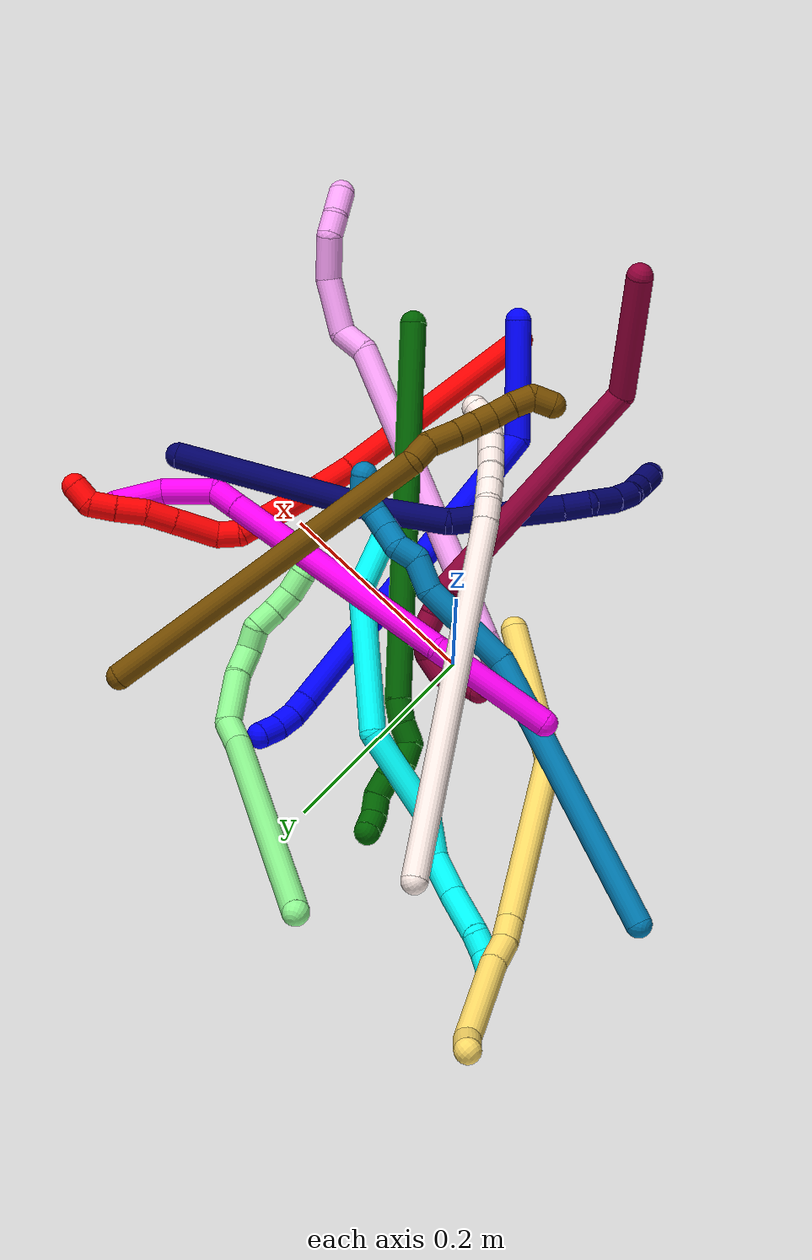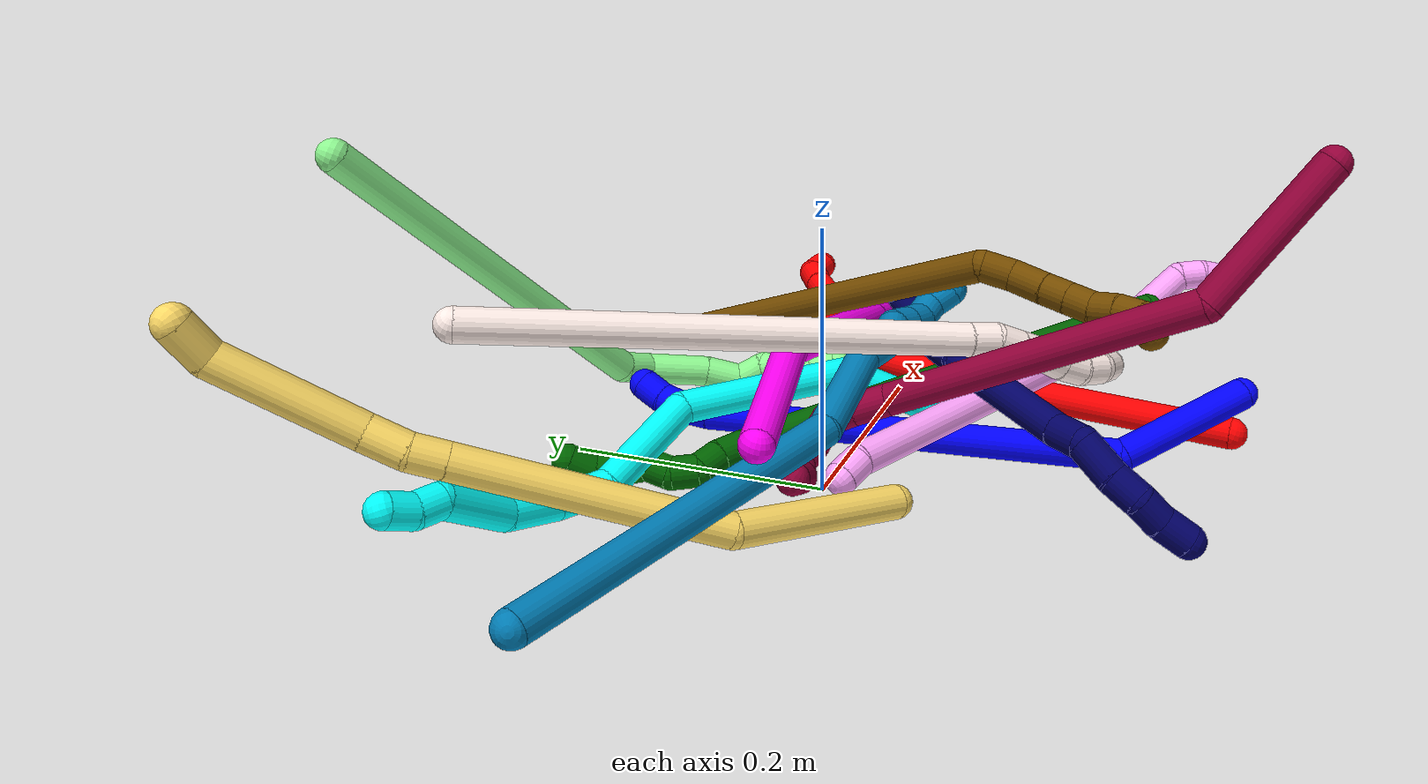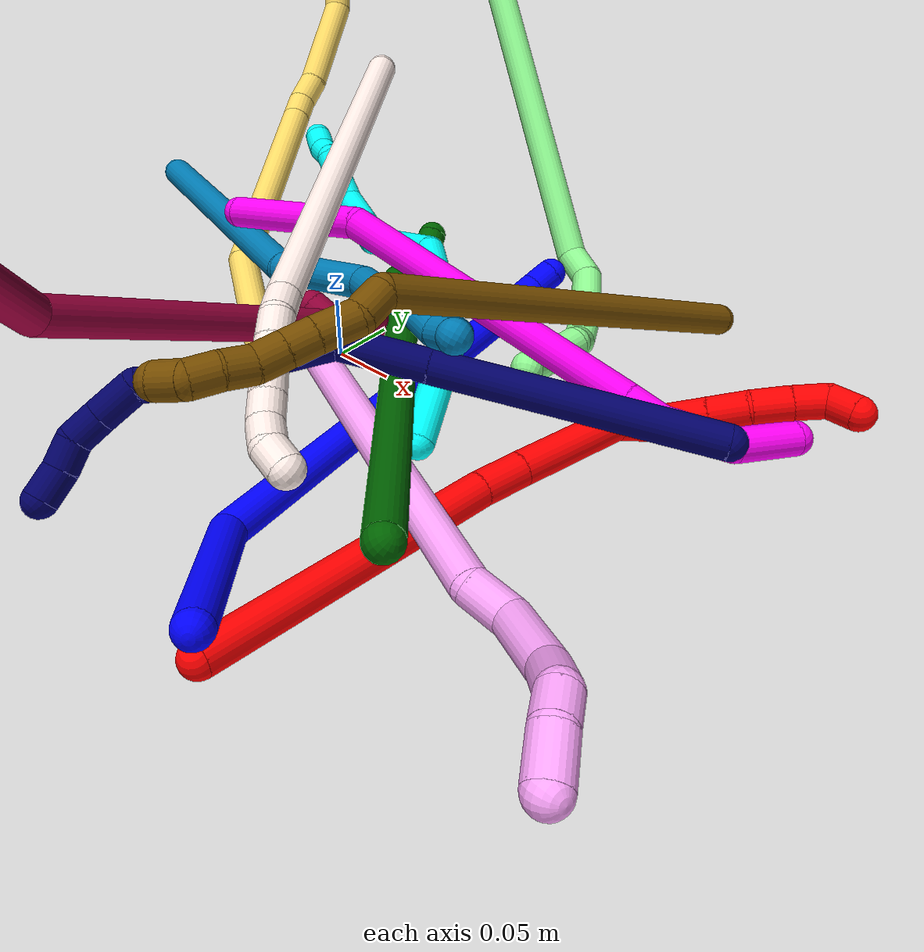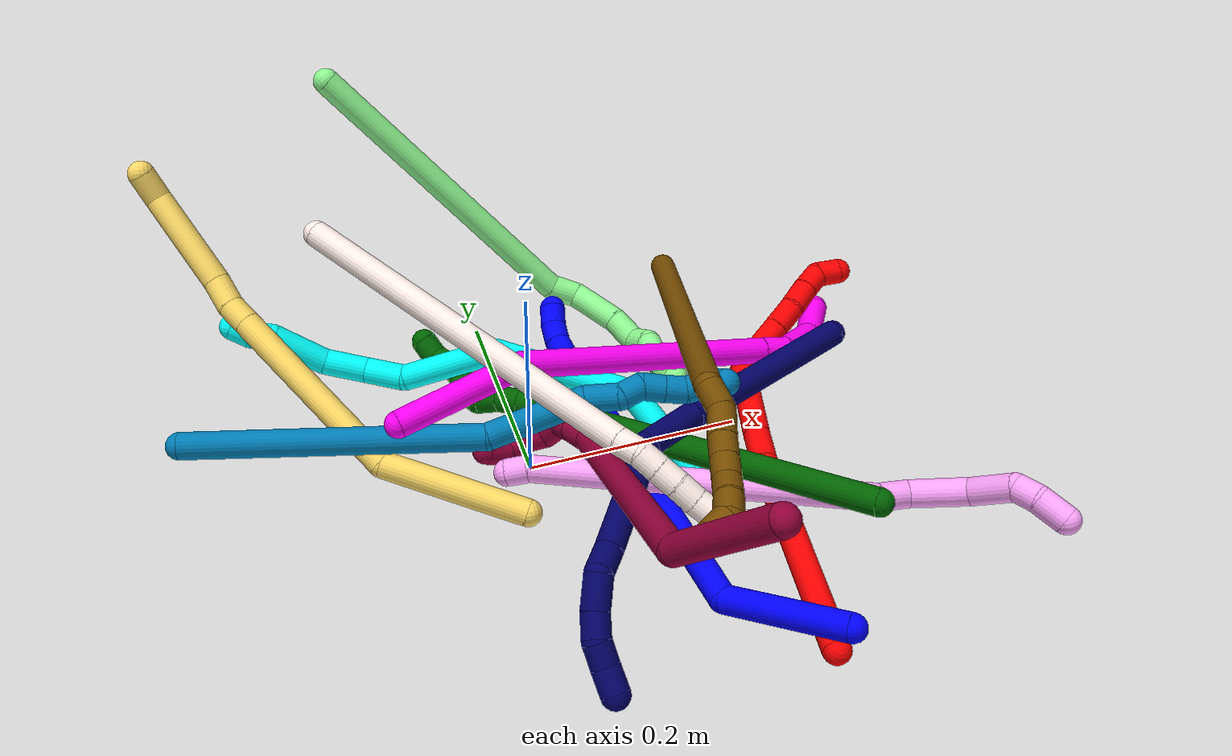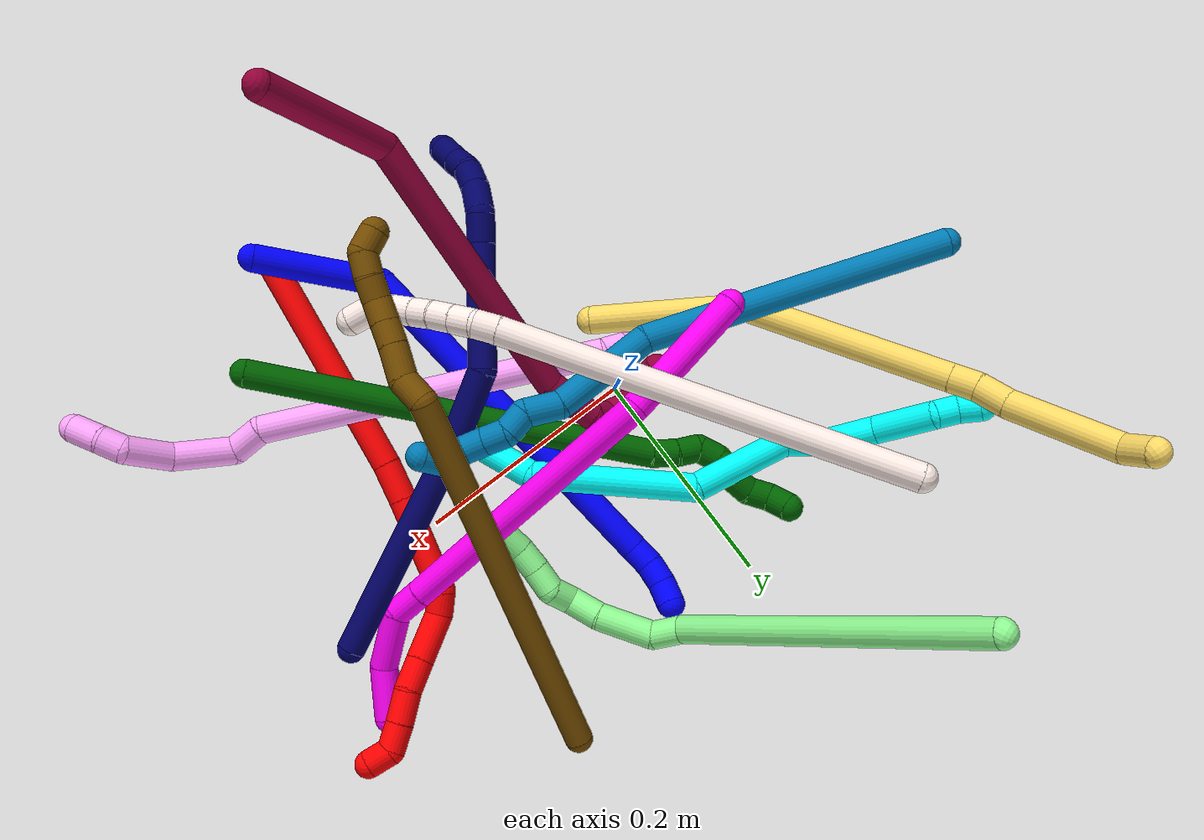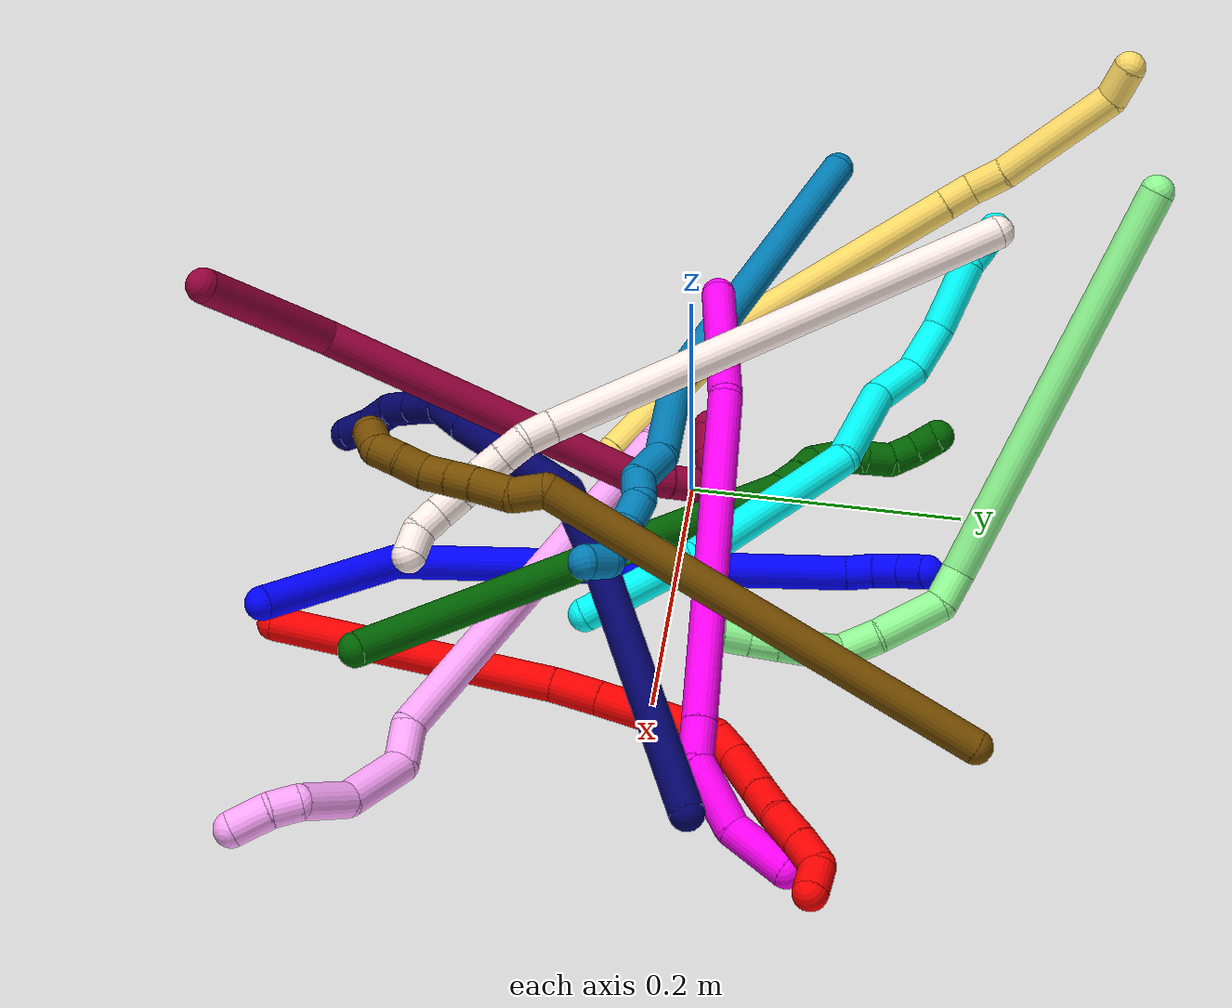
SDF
<sdf version="1.7">
 <world name="default">
  <plugin name="TubeGeneratorPlugin" filename="libtube_generator_plugin.so"/>
  <model name="photoneo_s_sensor">
   <static>1</static>
   <pose>0 0 2 1.57079 1.57079 3.14159</pose>
   <link name="link">
    <inertial><mass>0.1</mass></inertial>
    <sensor name="sensor" type="depth">
     <update_rate>30</update_rate>
     <camera>
      <horizontal_fov>1.22</horizontal_fov>
      <image><width>1920</width><height>1200</height><format>B8G8R8</format></image>
      <clip><near>0.1</near><far>4</far></clip>
      <depth_camera><output>points</output></depth_camera>
     </camera>
     <plugin name="camera_plugin" filename="libgazebo_ros_depth_camera.so">
      <baseline>0.2</baseline>
      <alwaysOn>1</alwaysOn>
      <updateRate>0.0</updateRate>
      <cameraName>camera_ir</cameraName>
      <imageTopicName>/camera/color/image_raw</imageTopicName>
      <cameraInfoTopicName>/camera/color/camera_info</cameraInfoTopicName>
      <depthImageTopicName>/camera/depth/image_raw</depthImageTopicName>
      <depthImageCameraInfoTopicName>/camera/depth/camera_info</depthImageCameraInfoTopicName>
      <pointCloudTopicName>/camera/depth/points</pointCloudTopicName>
      <frameName>fr_optical</frameName>
      <pointCloudCutoff>0.1</pointCloudCutoff>
      <pointCloudCutoffMax>2.0</pointCloudCutoffMax>
      <distortionK1>0</distortionK1>
      <distortionK2>0</distortionK2>
      <distortionK3>0</distortionK3>
      <distortionT1>0</distortionT1>
      <distortionT2>0</distortionT2>
      <CxPrime>0</CxPrime>
      <Cx>0</Cx>
      <Cy>0</Cy>
      <focalLength>0</focalLength>
      <hackBaseline>0</hackBaseline>
     </plugin>
    </sensor>
   </link>
  </model>
  <gravity>0 0 -9.8</gravity>
  <magnetic_field>6e-06 2.3e-05 -4.2e-05</magnetic_field>
  <atmosphere type="adiabatic"/>
  <physics name="default_physics" default="0" type="ode">
   <max_step_size>0.003</max_step_size>
   <real_time_factor>1</real_time_factor>
   <real_time_update_rate>1000</real_time_update_rate>
   <max_contacts>10000</max_contacts>
   <ode>
    <solver>
     <type>quick</type>
     <iters>100</iters>
     <sor>1.3</sor>
     <use_dynamic_moi_rescaling>0</use_dynamic_moi_rescaling>
    </solver>
    <constraints>
     <contact_max_correcting_vel>0</contact_max_correcting_vel>
     <contact_surface_layer>0.001</contact_surface_layer>
     <cfm>0</cfm>
     <erp>0.2</erp>
    </constraints>
   </ode>
  </physics>
  <scene><ambient>0.4 0.4 0.4 1</ambient><background>0.7 0.7 0.7 1</background><shadows>0</shadows></scene>
  <audio><device>default</device></audio>
  <spherical_coordinates>
   <surface_model>EARTH_WGS84</surface_model>
   <latitude_deg>0</latitude_deg>
   <longitude_deg>0</longitude_deg>
   <elevation>0</elevation>
   <heading_deg>0</heading_deg>
  </spherical_coordinates>
  <model name="bin">
   <static>1</static>
   <link name="bottom">
    <collision name="collision-bottom">
     <pose>0 0 -0.01 0 -0 0</pose>
     <geometry><box><size>0.8 0.6 0.02</size></box></geometry>
     <surface>
      <friction><ode><mu>100</mu><mu2>100</mu2></ode></friction>
      <contact><collide_bitmask>65535</collide_bitmask></contact>
     </surface>
    </collision>
   </link>
   <link name="west_wall">
    <collision name="collision-west_wall">
     <pose>-0.41 0 0.1 0 -0 0</pose>
     <geometry><box><size>0.02 0.6 0.2</size></box></geometry>
     <surface>
      <friction><ode><mu>100</mu><mu2>100</mu2></ode></friction>
      <contact><collide_bitmask>65535</collide_bitmask></contact>
     </surface>
    </collision>
   </link>
   <link name="east_wall">
    <collision name="collision-east_wall">
     <pose>0.41 0 0.1 0 -0 0</pose>
     <geometry><box><size>0.02 0.6 0.2</size></box></geometry>
     <surface>
      <friction><ode><mu>100</mu><mu2>100</mu2></ode></friction>
      <contact><collide_bitmask>65535</collide_bitmask></contact>
     </surface>
    </collision>
   </link>
   <link name="south_wall">
    <collision name="collision-south_wall">
     <pose>0 -0.31 0.1 0 -0 0</pose>
     <geometry><box><size>0.8 0.02 0.2</size></box></geometry>
     <surface>
      <friction><ode><mu>100</mu><mu2>100</mu2></ode></friction>
      <contact><collide_bitmask>65535</collide_bitmask></contact>
     </surface>
    </collision>
   </link>
   <link name="north_wall">
    <collision name="collision-north_wall">
     <pose>0 0.31 0.1 0 -0 0</pose>
     <geometry><box><size>0.8 0.02 0.2</size></box></geometry>
     <surface>
      <friction><ode><mu>100</mu><mu2>100</mu2></ode></friction>
      <contact><collide_bitmask>65535</collide_bitmask></contact>
     </surface>
    </collision>
   </link>
  </model>
  <model name="1">
   <static>0</static>
   <link name="1">
    <collision name="collision-cylinder-e_1_1_4">
     <pose>-0.002907 -0.000421 -0.056557 3.13416 -0.051359 -2.85405</pose>
     <geometry><cylinder><radius>0.0125</radius><length>0.113266</length></cylinder></geometry>
     <surface>
      <friction><ode><mu>1.16</mu><mu2>1.16</mu2><slip1>0</slip1><slip2>0</slip2></ode></friction>
      <contact><ode><kp>1e+06</kp><kd>1</kd><max_vel>0</max_vel><min_depth>0.001</min_depth></ode></contact>
     </surface>
    </collision>
    <visual name="visual-cylinder-e_1_1_4">
     <pose>-0.002907 -0.000421 -0.056557 3.13416 -0.051359 -2.85405</pose>
     <geometry><cylinder><radius>0.0125</radius><length>0.113266</length></cylinder></geometry>
     <material><ambient>0 0 1 1</ambient></material>
    </visual>
    <collision name="collision-cylinder-e_2_4_5">
     <pose>-0.005925 0.103112 -0.238619 -2.44985 -0.000676 0.001877</pose>
     <geometry><cylinder><radius>0.0125</radius><length>0.325933</length></cylinder></geometry>
     <surface>
      <friction><ode><mu>1.16</mu><mu2>1.16</mu2><slip1>0</slip1><slip2>0</slip2></ode></friction>
      <contact><ode><kp>1e+06</kp><kd>1</kd><max_vel>0</max_vel><min_depth>0.001</min_depth></ode></contact>
     </surface>
    </collision>
    <visual name="visual-cylinder-e_2_4_5">
     <pose>-0.005925 0.103112 -0.238619 -2.44985 -0.000676 0.001877</pose>
     <geometry><cylinder><radius>0.0125</radius><length>0.325933</length></cylinder></geometry>
     <material><ambient>0 0 1 1</ambient></material>
    </visual>
    <collision name="collision-cylinder-e_3_5_6">
     <pose>-0.007455 0.213948 -0.371365 -2.38153 -0.141163 0.350352</pose>
     <geometry><cylinder><radius>0.0125</radius><length>0.020178</length></cylinder></geometry>
     <surface>
      <friction><ode><mu>1.16</mu><mu2>1.16</mu2><slip1>0</slip1><slip2>0</slip2></ode></friction>
      <contact><ode><kp>1e+06</kp><kd>1</kd><max_vel>0</max_vel><min_depth>0.001</min_depth></ode></contact>
     </surface>
    </collision>
    <visual name="visual-cylinder-e_3_5_6">
     <pose>-0.007455 0.213948 -0.371365 -2.38153 -0.141163 0.350352</pose>
     <geometry><cylinder><radius>0.0125</radius><length>0.020178</length></cylinder></geometry>
     <material><ambient>0 0 1 1</ambient></material>
    </visual>
    <collision name="collision-cylinder-e_4_6_7">
     <pose>-0.010122 0.229074 -0.384244 -2.17075 -0.124343 0.23493</pose>
     <geometry><cylinder><radius>0.0125</radius><length>0.020132</length></cylinder></geometry>
     <surface>
      <friction><ode><mu>1.16</mu><mu2>1.16</mu2><slip1>0</slip1><slip2>0</slip2></ode></friction>
      <contact><ode><kp>1e+06</kp><kd>1</kd><max_vel>0</max_vel><min_depth>0.001</min_depth></ode></contact>
     </surface>
    </collision>
    <visual name="visual-cylinder-e_4_6_7">
     <pose>-0.010122 0.229074 -0.384244 -2.17075 -0.124343 0.23493</pose>
     <geometry><cylinder><radius>0.0125</radius><length>0.020132</length></cylinder></geometry>
     <material><ambient>0 0 1 1</ambient></material>
    </visual>
    <collision name="collision-cylinder-e_5_7_2">
     <pose>-0.013167 0.246671 -0.39366 -1.95458 -0.176178 0.260338</pose>
     <geometry><cylinder><radius>0.0125</radius><length>0.020491</length></cylinder></geometry>
     <surface>
      <friction><ode><mu>1.16</mu><mu2>1.16</mu2><slip1>0</slip1><slip2>0</slip2></ode></friction>
      <contact><ode><kp>1e+06</kp><kd>1</kd><max_vel>0</max_vel><min_depth>0.001</min_depth></ode></contact>
     </surface>
    </collision>
    <visual name="visual-cylinder-e_5_7_2">
     <pose>-0.013167 0.246671 -0.39366 -1.95458 -0.176178 0.260338</pose>
     <geometry><cylinder><radius>0.0125</radius><length>0.020491</length></cylinder></geometry>
     <material><ambient>0 0 1 1</ambient></material>
    </visual>
    <collision name="collision-sphere-2">
     <pose>-0.014962 0.256024 -0.397437 0 -0 0</pose>
     <geometry><sphere><radius>0.0125</radius></sphere></geometry>
     <surface>
      <friction><ode><mu>1.16</mu><mu2>1.16</mu2><slip1>0</slip1><slip2>0</slip2></ode></friction>
      <contact><ode><kp>1e+06</kp><kd>1</kd><max_vel>0</max_vel><min_depth>0.001</min_depth></ode></contact>
     </surface>
    </collision>
    <visual name="visual-sphere-2">
     <pose>-0.014962 0.256024 -0.397437 0 -0 0</pose>
     <geometry><sphere><radius>0.0125</radius></sphere></geometry>
     <material><ambient>0 0 1 1</ambient></material>
    </visual>
    <collision name="collision-sphere-7">
     <pose>-0.011371 0.237318 -0.389884 0 -0 0</pose>
     <geometry><sphere><radius>0.0125</radius></sphere></geometry>
     <surface>
      <friction><ode><mu>1.16</mu><mu2>1.16</mu2><slip1>0</slip1><slip2>0</slip2></ode></friction>
      <contact><ode><kp>1e+06</kp><kd>1</kd><max_vel>0</max_vel><min_depth>0.001</min_depth></ode></contact>
     </surface>
    </collision>
    <visual name="visual-sphere-7">
     <pose>-0.011371 0.237318 -0.389884 0 -0 0</pose>
     <geometry><sphere><radius>0.0125</radius></sphere></geometry>
     <material><ambient>0 0 1 1</ambient></material>
    </visual>
    <collision name="collision-sphere-6">
     <pose>-0.008874 0.22083 -0.378605 0 -0 0</pose>
     <geometry><sphere><radius>0.0125</radius></sphere></geometry>
     <surface>
      <friction><ode><mu>1.16</mu><mu2>1.16</mu2><slip1>0</slip1><slip2>0</slip2></ode></friction>
      <contact><ode><kp>1e+06</kp><kd>1</kd><max_vel>0</max_vel><min_depth>0.001</min_depth></ode></contact>
     </surface>
    </collision>
    <visual name="visual-sphere-6">
     <pose>-0.008874 0.22083 -0.378605 0 -0 0</pose>
     <geometry><sphere><radius>0.0125</radius></sphere></geometry>
     <material><ambient>0 0 1 1</ambient></material>
    </visual>
    <collision name="collision-sphere-5">
     <pose>-0.006035 0.207066 -0.364125 0 -0 0</pose>
     <geometry><sphere><radius>0.0125</radius></sphere></geometry>
     <surface>
      <friction><ode><mu>1.16</mu><mu2>1.16</mu2><slip1>0</slip1><slip2>0</slip2></ode></friction>
      <contact><ode><kp>1e+06</kp><kd>1</kd><max_vel>0</max_vel><min_depth>0.001</min_depth></ode></contact>
     </surface>
    </collision>
    <visual name="visual-sphere-5">
     <pose>-0.006035 0.207066 -0.364125 0 -0 0</pose>
     <geometry><sphere><radius>0.0125</radius></sphere></geometry>
     <material><ambient>0 0 1 1</ambient></material>
    </visual>
    <collision name="collision-sphere-1">
     <geometry><sphere><radius>0.0125</radius></sphere></geometry>
     <surface>
      <friction><ode><mu>1.16</mu><mu2>1.16</mu2><slip1>0</slip1><slip2>0</slip2></ode></friction>
      <contact><ode><kp>1e+06</kp><kd>1</kd><max_vel>0</max_vel><min_depth>0.001</min_depth></ode></contact>
     </surface>
    </collision>
    <visual name="visual-sphere-1">
     <geometry><sphere><radius>0.0125</radius></sphere></geometry>
     <material><ambient>0 0 1 1</ambient></material>
    </visual>
    <collision name="collision-sphere-4">
     <pose>-0.005815 -0.000841 -0.113113 0 -0 0</pose>
     <geometry><sphere><radius>0.0125</radius></sphere></geometry>
     <surface>
      <friction><ode><mu>1.16</mu><mu2>1.16</mu2><slip1>0</slip1><slip2>0</slip2></ode></friction>
      <contact><ode><kp>1e+06</kp><kd>1</kd><max_vel>0</max_vel><min_depth>0.001</min_depth></ode></contact>
     </surface>
    </collision>
    <visual name="visual-sphere-4">
     <pose>-0.005815 -0.000841 -0.113113 0 -0 0</pose>
     <geometry><sphere><radius>0.0125</radius></sphere></geometry>
     <material><ambient>0 0 1 1</ambient></material>
    </visual>
    <inertial>
     <pose>-0.005769 0.095087 -0.214951 0 -0 0</pose>
     <mass>0.5</mass>
     <inertia>
      <ixx>0.002752</ixx>
      <ixy>0</ixy>
      <ixz>0</ixz>
      <iyy>-0.002123</iyy>
      <iyz>0</iyz>
      <izz>-0.001873</izz>
     </inertia>
    </inertial>
   </link>
   <pose>0.182664 -0.27986 0.042795 0.877884 1.04889 0.107894</pose>
  </model>
  <model name="2">
   <static>0</static>
   <link name="2">
    <collision name="collision-cylinder-e_1_1_4">
     <pose>0.028957 0.095542 0.029969 -1.26684 0.281508 -0.20736</pose>
     <geometry><cylinder><radius>0.0125</radius><length>0.20847</length></cylinder></geometry>
     <surface>
      <friction><ode><mu>1.16</mu><mu2>1.16</mu2><slip1>0</slip1><slip2>0</slip2></ode></friction>
      <contact><ode><kp>1e+06</kp><kd>1</kd><max_vel>0</max_vel><min_depth>0.001</min_depth></ode></contact>
     </surface>
    </collision>
    <visual name="visual-cylinder-e_1_1_4">
     <pose>0.028957 0.095542 0.029969 -1.26684 0.281508 -0.20736</pose>
     <geometry><cylinder><radius>0.0125</radius><length>0.20847</length></cylinder></geometry>
     <material><ambient>1 0 0 1</ambient></material>
    </visual>
    <collision name="collision-cylinder-e_2_4_5">
     <pose>0.061309 0.207305 0.064799 -1.27965 0.197874 -0.147487</pose>
     <geometry><cylinder><radius>0.0125</radius><length>0.034541</length></cylinder></geometry>
     <surface>
      <friction><ode><mu>1.16</mu><mu2>1.16</mu2><slip1>0</slip1><slip2>0</slip2></ode></friction>
      <contact><ode><kp>1e+06</kp><kd>1</kd><max_vel>0</max_vel><min_depth>0.001</min_depth></ode></contact>
     </surface>
    </collision>
    <visual name="visual-cylinder-e_2_4_5">
     <pose>0.061309 0.207305 0.064799 -1.27965 0.197874 -0.147487</pose>
     <geometry><cylinder><radius>0.0125</radius><length>0.034541</length></cylinder></geometry>
     <material><ambient>1 0 0 1</ambient></material>
    </visual>
    <collision name="collision-cylinder-e_3_5_6">
     <pose>0.072048 0.265115 0.081263 -1.29873 0.168467 -0.128029</pose>
     <geometry><cylinder><radius>0.0125</radius><length>0.087596</length></cylinder></geometry>
     <surface>
      <friction><ode><mu>1.16</mu><mu2>1.16</mu2><slip1>0</slip1><slip2>0</slip2></ode></friction>
      <contact><ode><kp>1e+06</kp><kd>1</kd><max_vel>0</max_vel><min_depth>0.001</min_depth></ode></contact>
     </surface>
    </collision>
    <visual name="visual-cylinder-e_3_5_6">
     <pose>0.072048 0.265115 0.081263 -1.29873 0.168467 -0.128029</pose>
     <geometry><cylinder><radius>0.0125</radius><length>0.087596</length></cylinder></geometry>
     <material><ambient>1 0 0 1</ambient></material>
    </visual>
    <collision name="collision-cylinder-e_4_6_7">
     <pose>0.075378 0.31647 0.095901 -1.26939 -0.373999 0.276861</pose>
     <geometry><cylinder><radius>0.0125</radius><length>0.021969</length></cylinder></geometry>
     <surface>
      <friction><ode><mu>1.16</mu><mu2>1.16</mu2><slip1>0</slip1><slip2>0</slip2></ode></friction>
      <contact><ode><kp>1e+06</kp><kd>1</kd><max_vel>0</max_vel><min_depth>0.001</min_depth></ode></contact>
     </surface>
    </collision>
    <visual name="visual-cylinder-e_4_6_7">
     <pose>0.075378 0.31647 0.095901 -1.26939 -0.373999 0.276861</pose>
     <geometry><cylinder><radius>0.0125</radius><length>0.021969</length></cylinder></geometry>
     <material><ambient>1 0 0 1</ambient></material>
    </visual>
    <collision name="collision-cylinder-e_5_7_8">
     <pose>0.060769 0.345094 0.094664 -1.79362 -0.501278 0.620354</pose>
     <geometry><cylinder><radius>0.0125</radius><length>0.044102</length></cylinder></geometry>
     <surface>
      <friction><ode><mu>1.16</mu><mu2>1.16</mu2><slip1>0</slip1><slip2>0</slip2></ode></friction>
      <contact><ode><kp>1e+06</kp><kd>1</kd><max_vel>0</max_vel><min_depth>0.001</min_depth></ode></contact>
     </surface>
    </collision>
    <visual name="visual-cylinder-e_5_7_8">
     <pose>0.060769 0.345094 0.094664 -1.79362 -0.501278 0.620354</pose>
     <geometry><cylinder><radius>0.0125</radius><length>0.044102</length></cylinder></geometry>
     <material><ambient>1 0 0 1</ambient></material>
    </visual>
    <collision name="collision-cylinder-e_6_8_9">
     <pose>0.043485 0.376057 0.087766 -1.78432 -0.495068 0.607382</pose>
     <geometry><cylinder><radius>0.0125</radius><length>0.02815</length></cylinder></geometry>
     <surface>
      <friction><ode><mu>1.16</mu><mu2>1.16</mu2><slip1>0</slip1><slip2>0</slip2></ode></friction>
      <contact><ode><kp>1e+06</kp><kd>1</kd><max_vel>0</max_vel><min_depth>0.001</min_depth></ode></contact>
     </surface>
    </collision>
    <visual name="visual-cylinder-e_6_8_9">
     <pose>0.043485 0.376057 0.087766 -1.78432 -0.495068 0.607382</pose>
     <geometry><cylinder><radius>0.0125</radius><length>0.02815</length></cylinder></geometry>
     <material><ambient>1 0 0 1</ambient></material>
    </visual>
    <collision name="collision-cylinder-e_7_9_10">
     <pose>0.030937 0.401162 0.085182 -1.5677 -0.42361 0.422341</pose>
     <geometry><cylinder><radius>0.0125</radius><length>0.028522</length></cylinder></geometry>
     <surface>
      <friction><ode><mu>1.16</mu><mu2>1.16</mu2><slip1>0</slip1><slip2>0</slip2></ode></friction>
      <contact><ode><kp>1e+06</kp><kd>1</kd><max_vel>0</max_vel><min_depth>0.001</min_depth></ode></contact>
     </surface>
    </collision>
    <visual name="visual-cylinder-e_7_9_10">
     <pose>0.030937 0.401162 0.085182 -1.5677 -0.42361 0.422341</pose>
     <geometry><cylinder><radius>0.0125</radius><length>0.028522</length></cylinder></geometry>
     <material><ambient>1 0 0 1</ambient></material>
    </visual>
    <collision name="collision-cylinder-e_8_10_11">
     <pose>0.019263 0.424979 0.085133 -1.57902 -0.493018 0.496924</pose>
     <geometry><cylinder><radius>0.0125</radius><length>0.024559</length></cylinder></geometry>
     <surface>
      <friction><ode><mu>1.16</mu><mu2>1.16</mu2><slip1>0</slip1><slip2>0</slip2></ode></friction>
      <contact><ode><kp>1e+06</kp><kd>1</kd><max_vel>0</max_vel><min_depth>0.001</min_depth></ode></contact>
     </surface>
    </collision>
    <visual name="visual-cylinder-e_8_10_11">
     <pose>0.019263 0.424979 0.085133 -1.57902 -0.493018 0.496924</pose>
     <geometry><cylinder><radius>0.0125</radius><length>0.024559</length></cylinder></geometry>
     <material><ambient>1 0 0 1</ambient></material>
    </visual>
    <collision name="collision-cylinder-e_9_11_2">
     <pose>0.003183 0.439591 0.083568 -1.94165 -1.19321 1.56357</pose>
     <geometry><cylinder><radius>0.0125</radius><length>0.022091</length></cylinder></geometry>
     <surface>
      <friction><ode><mu>1.16</mu><mu2>1.16</mu2><slip1>0</slip1><slip2>0</slip2></ode></friction>
      <contact><ode><kp>1e+06</kp><kd>1</kd><max_vel>0</max_vel><min_depth>0.001</min_depth></ode></contact>
     </surface>
    </collision>
    <visual name="visual-cylinder-e_9_11_2">
     <pose>0.003183 0.439591 0.083568 -1.94165 -1.19321 1.56357</pose>
     <geometry><cylinder><radius>0.0125</radius><length>0.022091</length></cylinder></geometry>
     <material><ambient>1 0 0 1</ambient></material>
    </visual>
    <collision name="collision-sphere-2">
     <pose>-0.007084 0.443386 0.082092 0 -0 0</pose>
     <geometry><sphere><radius>0.0125</radius></sphere></geometry>
     <surface>
      <friction><ode><mu>1.16</mu><mu2>1.16</mu2><slip1>0</slip1><slip2>0</slip2></ode></friction>
      <contact><ode><kp>1e+06</kp><kd>1</kd><max_vel>0</max_vel><min_depth>0.001</min_depth></ode></contact>
     </surface>
    </collision>
    <visual name="visual-sphere-2">
     <pose>-0.007084 0.443386 0.082092 0 -0 0</pose>
     <geometry><sphere><radius>0.0125</radius></sphere></geometry>
     <material><ambient>1 0 0 1</ambient></material>
    </visual>
    <collision name="collision-sphere-11">
     <pose>0.013451 0.435796 0.085044 0 -0 0</pose>
     <geometry><sphere><radius>0.0125</radius></sphere></geometry>
     <surface>
      <friction><ode><mu>1.16</mu><mu2>1.16</mu2><slip1>0</slip1><slip2>0</slip2></ode></friction>
      <contact><ode><kp>1e+06</kp><kd>1</kd><max_vel>0</max_vel><min_depth>0.001</min_depth></ode></contact>
     </surface>
    </collision>
    <visual name="visual-sphere-11">
     <pose>0.013451 0.435796 0.085044 0 -0 0</pose>
     <geometry><sphere><radius>0.0125</radius></sphere></geometry>
     <material><ambient>1 0 0 1</ambient></material>
    </visual>
    <collision name="collision-sphere-10">
     <pose>0.025074 0.414162 0.085222 0 -0 0</pose>
     <geometry><sphere><radius>0.0125</radius></sphere></geometry>
     <surface>
      <friction><ode><mu>1.16</mu><mu2>1.16</mu2><slip1>0</slip1><slip2>0</slip2></ode></friction>
      <contact><ode><kp>1e+06</kp><kd>1</kd><max_vel>0</max_vel><min_depth>0.001</min_depth></ode></contact>
     </surface>
    </collision>
    <visual name="visual-sphere-10">
     <pose>0.025074 0.414162 0.085222 0 -0 0</pose>
     <geometry><sphere><radius>0.0125</radius></sphere></geometry>
     <material><ambient>1 0 0 1</ambient></material>
    </visual>
    <collision name="collision-sphere-9">
     <pose>0.036799 0.388161 0.085141 0 -0 0</pose>
     <geometry><sphere><radius>0.0125</radius></sphere></geometry>
     <surface>
      <friction><ode><mu>1.16</mu><mu2>1.16</mu2><slip1>0</slip1><slip2>0</slip2></ode></friction>
      <contact><ode><kp>1e+06</kp><kd>1</kd><max_vel>0</max_vel><min_depth>0.001</min_depth></ode></contact>
     </surface>
    </collision>
    <visual name="visual-sphere-9">
     <pose>0.036799 0.388161 0.085141 0 -0 0</pose>
     <geometry><sphere><radius>0.0125</radius></sphere></geometry>
     <material><ambient>1 0 0 1</ambient></material>
    </visual>
    <collision name="collision-sphere-4">
     <pose>0.057914 0.191084 0.059938 0 -0 0</pose>
     <geometry><sphere><radius>0.0125</radius></sphere></geometry>
     <surface>
      <friction><ode><mu>1.16</mu><mu2>1.16</mu2><slip1>0</slip1><slip2>0</slip2></ode></friction>
      <contact><ode><kp>1e+06</kp><kd>1</kd><max_vel>0</max_vel><min_depth>0.001</min_depth></ode></contact>
     </surface>
    </collision>
    <visual name="visual-sphere-4">
     <pose>0.057914 0.191084 0.059938 0 -0 0</pose>
     <geometry><sphere><radius>0.0125</radius></sphere></geometry>
     <material><ambient>1 0 0 1</ambient></material>
    </visual>
    <collision name="collision-sphere-1">
     <geometry><sphere><radius>0.0125</radius></sphere></geometry>
     <surface>
      <friction><ode><mu>1.16</mu><mu2>1.16</mu2><slip1>0</slip1><slip2>0</slip2></ode></friction>
      <contact><ode><kp>1e+06</kp><kd>1</kd><max_vel>0</max_vel><min_depth>0.001</min_depth></ode></contact>
     </surface>
    </collision>
    <visual name="visual-sphere-1">
     <geometry><sphere><radius>0.0125</radius></sphere></geometry>
     <material><ambient>1 0 0 1</ambient></material>
    </visual>
    <collision name="collision-sphere-8">
     <pose>0.050172 0.363954 0.09039 0 -0 0</pose>
     <geometry><sphere><radius>0.0125</radius></sphere></geometry>
     <surface>
      <friction><ode><mu>1.16</mu><mu2>1.16</mu2><slip1>0</slip1><slip2>0</slip2></ode></friction>
      <contact><ode><kp>1e+06</kp><kd>1</kd><max_vel>0</max_vel><min_depth>0.001</min_depth></ode></contact>
     </surface>
    </collision>
    <visual name="visual-sphere-8">
     <pose>0.050172 0.363954 0.09039 0 -0 0</pose>
     <geometry><sphere><radius>0.0125</radius></sphere></geometry>
     <material><ambient>1 0 0 1</ambient></material>
    </visual>
    <collision name="collision-sphere-5">
     <pose>0.064704 0.223525 0.06966 0 -0 0</pose>
     <geometry><sphere><radius>0.0125</radius></sphere></geometry>
     <surface>
      <friction><ode><mu>1.16</mu><mu2>1.16</mu2><slip1>0</slip1><slip2>0</slip2></ode></friction>
      <contact><ode><kp>1e+06</kp><kd>1</kd><max_vel>0</max_vel><min_depth>0.001</min_depth></ode></contact>
     </surface>
    </collision>
    <visual name="visual-sphere-5">
     <pose>0.064704 0.223525 0.06966 0 -0 0</pose>
     <geometry><sphere><radius>0.0125</radius></sphere></geometry>
     <material><ambient>1 0 0 1</ambient></material>
    </visual>
    <collision name="collision-sphere-6">
     <pose>0.079391 0.306705 0.092866 0 -0 0</pose>
     <geometry><sphere><radius>0.0125</radius></sphere></geometry>
     <surface>
      <friction><ode><mu>1.16</mu><mu2>1.16</mu2><slip1>0</slip1><slip2>0</slip2></ode></friction>
      <contact><ode><kp>1e+06</kp><kd>1</kd><max_vel>0</max_vel><min_depth>0.001</min_depth></ode></contact>
     </surface>
    </collision>
    <visual name="visual-sphere-6">
     <pose>0.079391 0.306705 0.092866 0 -0 0</pose>
     <geometry><sphere><radius>0.0125</radius></sphere></geometry>
     <material><ambient>1 0 0 1</ambient></material>
    </visual>
    <collision name="collision-sphere-7">
     <pose>0.071365 0.326234 0.098937 0 -0 0</pose>
     <geometry><sphere><radius>0.0125</radius></sphere></geometry>
     <surface>
      <friction><ode><mu>1.16</mu><mu2>1.16</mu2><slip1>0</slip1><slip2>0</slip2></ode></friction>
      <contact><ode><kp>1e+06</kp><kd>1</kd><max_vel>0</max_vel><min_depth>0.001</min_depth></ode></contact>
     </surface>
    </collision>
    <visual name="visual-sphere-7">
     <pose>0.071365 0.326234 0.098937 0 -0 0</pose>
     <geometry><sphere><radius>0.0125</radius></sphere></geometry>
     <material><ambient>1 0 0 1</ambient></material>
    </visual>
    <inertial>
     <pose>0.042903 0.229298 0.061446 0 -0 0</pose>
     <mass>0.5</mass>
     <inertia>
      <ixx>0.000644</ixx>
      <ixy>0</ixy>
      <ixz>0</ixz>
      <iyy>0.000173</iyy>
      <iyz>0</iyz>
      <izz>-0.000984</izz>
     </inertia>
    </inertial>
   </link>
   <pose>0.175414 -0.275821 0.011491 2.88485 -0.182541 2.72829</pose>
  </model>
  <model name="3">
   <static>0</static>
   <link name="3">
    <collision name="collision-cylinder-e_1_1_4">
     <pose>-0.023869 0.014886 0.035081 -0.401315 -0.559553 0.116743</pose>
     <geometry><cylinder><radius>0.0125</radius><length>0.089933</length></cylinder></geometry>
     <surface>
      <friction><ode><mu>1.16</mu><mu2>1.16</mu2><slip1>0</slip1><slip2>0</slip2></ode></friction>
      <contact><ode><kp>1e+06</kp><kd>1</kd><max_vel>0</max_vel><min_depth>0.001</min_depth></ode></contact>
     </surface>
    </collision>
    <visual name="visual-cylinder-e_1_1_4">
     <pose>-0.023869 0.014886 0.035081 -0.401315 -0.559553 0.116743</pose>
     <geometry><cylinder><radius>0.0125</radius><length>0.089933</length></cylinder></geometry>
     <material><ambient>0.003922 1 0.996078 1</ambient></material>
    </visual>
    <collision name="collision-cylinder-e_2_4_5">
     <pose>-0.045337 0.051651 0.137304 -0.314996 0.033983 -0.005397</pose>
     <geometry><cylinder><radius>0.0125</radius><length>0.141315</length></cylinder></geometry>
     <surface>
      <friction><ode><mu>1.16</mu><mu2>1.16</mu2><slip1>0</slip1><slip2>0</slip2></ode></friction>
      <contact><ode><kp>1e+06</kp><kd>1</kd><max_vel>0</max_vel><min_depth>0.001</min_depth></ode></contact>
     </surface>
    </collision>
    <visual name="visual-cylinder-e_2_4_5">
     <pose>-0.045337 0.051651 0.137304 -0.314996 0.033983 -0.005397</pose>
     <geometry><cylinder><radius>0.0125</radius><length>0.141315</length></cylinder></geometry>
     <material><ambient>0.003922 1 0.996078 1</ambient></material>
    </visual>
    <collision name="collision-cylinder-e_3_5_6">
     <pose>-0.01648 0.090036 0.238063 -0.456447 0.615018 -0.147264</pose>
     <geometry><cylinder><radius>0.0125</radius><length>0.091706</length></cylinder></geometry>
     <surface>
      <friction><ode><mu>1.16</mu><mu2>1.16</mu2><slip1>0</slip1><slip2>0</slip2></ode></friction>
      <contact><ode><kp>1e+06</kp><kd>1</kd><max_vel>0</max_vel><min_depth>0.001</min_depth></ode></contact>
     </surface>
    </collision>
    <visual name="visual-cylinder-e_3_5_6">
     <pose>-0.01648 0.090036 0.238063 -0.456447 0.615018 -0.147264</pose>
     <geometry><cylinder><radius>0.0125</radius><length>0.091706</length></cylinder></geometry>
     <material><ambient>0.003922 1 0.996078 1</ambient></material>
    </visual>
    <collision name="collision-cylinder-e_4_6_7">
     <pose>0.012734 0.112885 0.290425 -0.326285 0.13847 -0.022828</pose>
     <geometry><cylinder><radius>0.0125</radius><length>0.039959</length></cylinder></geometry>
     <surface>
      <friction><ode><mu>1.16</mu><mu2>1.16</mu2><slip1>0</slip1><slip2>0</slip2></ode></friction>
      <contact><ode><kp>1e+06</kp><kd>1</kd><max_vel>0</max_vel><min_depth>0.001</min_depth></ode></contact>
     </surface>
    </collision>
    <visual name="visual-cylinder-e_4_6_7">
     <pose>0.012734 0.112885 0.290425 -0.326285 0.13847 -0.022828</pose>
     <geometry><cylinder><radius>0.0125</radius><length>0.039959</length></cylinder></geometry>
     <material><ambient>0.003922 1 0.996078 1</ambient></material>
    </visual>
    <collision name="collision-cylinder-e_5_7_8">
     <pose>0.018486 0.132598 0.32508 -0.698813 0.143116 -0.052223</pose>
     <geometry><cylinder><radius>0.0125</radius><length>0.041994</length></cylinder></geometry>
     <surface>
      <friction><ode><mu>1.16</mu><mu2>1.16</mu2><slip1>0</slip1><slip2>0</slip2></ode></friction>
      <contact><ode><kp>1e+06</kp><kd>1</kd><max_vel>0</max_vel><min_depth>0.001</min_depth></ode></contact>
     </surface>
    </collision>
    <visual name="visual-cylinder-e_5_7_8">
     <pose>0.018486 0.132598 0.32508 -0.698813 0.143116 -0.052223</pose>
     <geometry><cylinder><radius>0.0125</radius><length>0.041994</length></cylinder></geometry>
     <material><ambient>0.003922 1 0.996078 1</ambient></material>
    </visual>
    <collision name="collision-cylinder-e_6_8_9">
     <pose>0.018813 0.168143 0.357046 -0.944161 -0.097126 0.04962</pose>
     <geometry><cylinder><radius>0.0125</radius><length>0.055015</length></cylinder></geometry>
     <surface>
      <friction><ode><mu>1.16</mu><mu2>1.16</mu2><slip1>0</slip1><slip2>0</slip2></ode></friction>
      <contact><ode><kp>1e+06</kp><kd>1</kd><max_vel>0</max_vel><min_depth>0.001</min_depth></ode></contact>
     </surface>
    </collision>
    <visual name="visual-cylinder-e_6_8_9">
     <pose>0.018813 0.168143 0.357046 -0.944161 -0.097126 0.04962</pose>
     <geometry><cylinder><radius>0.0125</radius><length>0.055015</length></cylinder></geometry>
     <material><ambient>0.003922 1 0.996078 1</ambient></material>
    </visual>
    <collision name="collision-cylinder-e_7_9_10">
     <pose>0.018863 0.195258 0.3814 -0.536832 0.274251 -0.075874</pose>
     <geometry><cylinder><radius>0.0125</radius><length>0.020065</length></cylinder></geometry>
     <surface>
      <friction><ode><mu>1.16</mu><mu2>1.16</mu2><slip1>0</slip1><slip2>0</slip2></ode></friction>
      <contact><ode><kp>1e+06</kp><kd>1</kd><max_vel>0</max_vel><min_depth>0.001</min_depth></ode></contact>
     </surface>
    </collision>
    <visual name="visual-cylinder-e_7_9_10">
     <pose>0.018863 0.195258 0.3814 -0.536832 0.274251 -0.075874</pose>
     <geometry><cylinder><radius>0.0125</radius><length>0.020065</length></cylinder></geometry>
     <material><ambient>0.003922 1 0.996078 1</ambient></material>
    </visual>
    <collision name="collision-cylinder-e_8_10_2">
     <pose>0.020899 0.206592 0.397366 -0.695145 -0.068127 0.024689</pose>
     <geometry><cylinder><radius>0.0125</radius><length>0.020013</length></cylinder></geometry>
     <surface>
      <friction><ode><mu>1.16</mu><mu2>1.16</mu2><slip1>0</slip1><slip2>0</slip2></ode></friction>
      <contact><ode><kp>1e+06</kp><kd>1</kd><max_vel>0</max_vel><min_depth>0.001</min_depth></ode></contact>
     </surface>
    </collision>
    <visual name="visual-cylinder-e_8_10_2">
     <pose>0.020899 0.206592 0.397366 -0.695145 -0.068127 0.024689</pose>
     <geometry><cylinder><radius>0.0125</radius><length>0.020013</length></cylinder></geometry>
     <material><ambient>0.003922 1 0.996078 1</ambient></material>
    </visual>
    <collision name="collision-sphere-2">
     <pose>0.020218 0.212986 0.405033 0 -0 0</pose>
     <geometry><sphere><radius>0.0125</radius></sphere></geometry>
     <surface>
      <friction><ode><mu>1.16</mu><mu2>1.16</mu2><slip1>0</slip1><slip2>0</slip2></ode></friction>
      <contact><ode><kp>1e+06</kp><kd>1</kd><max_vel>0</max_vel><min_depth>0.001</min_depth></ode></contact>
     </surface>
    </collision>
    <visual name="visual-sphere-2">
     <pose>0.020218 0.212986 0.405033 0 -0 0</pose>
     <geometry><sphere><radius>0.0125</radius></sphere></geometry>
     <material><ambient>0.003922 1 0.996078 1</ambient></material>
    </visual>
    <collision name="collision-sphere-10">
     <pose>0.02158 0.200197 0.389699 0 -0 0</pose>
     <geometry><sphere><radius>0.0125</radius></sphere></geometry>
     <surface>
      <friction><ode><mu>1.16</mu><mu2>1.16</mu2><slip1>0</slip1><slip2>0</slip2></ode></friction>
      <contact><ode><kp>1e+06</kp><kd>1</kd><max_vel>0</max_vel><min_depth>0.001</min_depth></ode></contact>
     </surface>
    </collision>
    <visual name="visual-sphere-10">
     <pose>0.02158 0.200197 0.389699 0 -0 0</pose>
     <geometry><sphere><radius>0.0125</radius></sphere></geometry>
     <material><ambient>0.003922 1 0.996078 1</ambient></material>
    </visual>
    <collision name="collision-sphere-9">
     <pose>0.016146 0.190319 0.373101 0 -0 0</pose>
     <geometry><sphere><radius>0.0125</radius></sphere></geometry>
     <surface>
      <friction><ode><mu>1.16</mu><mu2>1.16</mu2><slip1>0</slip1><slip2>0</slip2></ode></friction>
      <contact><ode><kp>1e+06</kp><kd>1</kd><max_vel>0</max_vel><min_depth>0.001</min_depth></ode></contact>
     </surface>
    </collision>
    <visual name="visual-sphere-9">
     <pose>0.016146 0.190319 0.373101 0 -0 0</pose>
     <geometry><sphere><radius>0.0125</radius></sphere></geometry>
     <material><ambient>0.003922 1 0.996078 1</ambient></material>
    </visual>
    <collision name="collision-sphere-4">
     <pose>-0.047737 0.029773 0.070162 0 -0 0</pose>
     <geometry><sphere><radius>0.0125</radius></sphere></geometry>
     <surface>
      <friction><ode><mu>1.16</mu><mu2>1.16</mu2><slip1>0</slip1><slip2>0</slip2></ode></friction>
      <contact><ode><kp>1e+06</kp><kd>1</kd><max_vel>0</max_vel><min_depth>0.001</min_depth></ode></contact>
     </surface>
    </collision>
    <visual name="visual-sphere-4">
     <pose>-0.047737 0.029773 0.070162 0 -0 0</pose>
     <geometry><sphere><radius>0.0125</radius></sphere></geometry>
     <material><ambient>0.003922 1 0.996078 1</ambient></material>
    </visual>
    <collision name="collision-sphere-1">
     <geometry><sphere><radius>0.0125</radius></sphere></geometry>
     <surface>
      <friction><ode><mu>1.16</mu><mu2>1.16</mu2><slip1>0</slip1><slip2>0</slip2></ode></friction>
      <contact><ode><kp>1e+06</kp><kd>1</kd><max_vel>0</max_vel><min_depth>0.001</min_depth></ode></contact>
     </surface>
    </collision>
    <visual name="visual-sphere-1">
     <geometry><sphere><radius>0.0125</radius></sphere></geometry>
     <material><ambient>0.003922 1 0.996078 1</ambient></material>
    </visual>
    <collision name="collision-sphere-8">
     <pose>0.021481 0.145967 0.340991 0 -0 0</pose>
     <geometry><sphere><radius>0.0125</radius></sphere></geometry>
     <surface>
      <friction><ode><mu>1.16</mu><mu2>1.16</mu2><slip1>0</slip1><slip2>0</slip2></ode></friction>
      <contact><ode><kp>1e+06</kp><kd>1</kd><max_vel>0</max_vel><min_depth>0.001</min_depth></ode></contact>
     </surface>
    </collision>
    <visual name="visual-sphere-8">
     <pose>0.021481 0.145967 0.340991 0 -0 0</pose>
     <geometry><sphere><radius>0.0125</radius></sphere></geometry>
     <material><ambient>0.003922 1 0.996078 1</ambient></material>
    </visual>
    <collision name="collision-sphere-5">
     <pose>-0.042936 0.073529 0.204447 0 -0 0</pose>
     <geometry><sphere><radius>0.0125</radius></sphere></geometry>
     <surface>
      <friction><ode><mu>1.16</mu><mu2>1.16</mu2><slip1>0</slip1><slip2>0</slip2></ode></friction>
      <contact><ode><kp>1e+06</kp><kd>1</kd><max_vel>0</max_vel><min_depth>0.001</min_depth></ode></contact>
     </surface>
    </collision>
    <visual name="visual-sphere-5">
     <pose>-0.042936 0.073529 0.204447 0 -0 0</pose>
     <geometry><sphere><radius>0.0125</radius></sphere></geometry>
     <material><ambient>0.003922 1 0.996078 1</ambient></material>
    </visual>
    <collision name="collision-sphere-6">
     <pose>0.009976 0.106543 0.27168 0 -0 0</pose>
     <geometry><sphere><radius>0.0125</radius></sphere></geometry>
     <surface>
      <friction><ode><mu>1.16</mu><mu2>1.16</mu2><slip1>0</slip1><slip2>0</slip2></ode></friction>
      <contact><ode><kp>1e+06</kp><kd>1</kd><max_vel>0</max_vel><min_depth>0.001</min_depth></ode></contact>
     </surface>
    </collision>
    <visual name="visual-sphere-6">
     <pose>0.009976 0.106543 0.27168 0 -0 0</pose>
     <geometry><sphere><radius>0.0125</radius></sphere></geometry>
     <material><ambient>0.003922 1 0.996078 1</ambient></material>
    </visual>
    <collision name="collision-sphere-7">
     <pose>0.015491 0.119228 0.309169 0 -0 0</pose>
     <geometry><sphere><radius>0.0125</radius></sphere></geometry>
     <surface>
      <friction><ode><mu>1.16</mu><mu2>1.16</mu2><slip1>0</slip1><slip2>0</slip2></ode></friction>
      <contact><ode><kp>1e+06</kp><kd>1</kd><max_vel>0</max_vel><min_depth>0.001</min_depth></ode></contact>
     </surface>
    </collision>
    <visual name="visual-sphere-7">
     <pose>0.015491 0.119228 0.309169 0 -0 0</pose>
     <geometry><sphere><radius>0.0125</radius></sphere></geometry>
     <material><ambient>0.003922 1 0.996078 1</ambient></material>
    </visual>
    <inertial>
     <pose>-0.013896 0.088553 0.209789 0 -0 0</pose>
     <mass>0.5</mass>
     <inertia>
      <ixx>0.000381</ixx>
      <ixy>0</ixy>
      <ixz>0</ixz>
      <iyy>0.00039</iyy>
      <iyz>0</iyz>
      <izz>-0.000124</izz>
     </inertia>
    </inertial>
   </link>
   <pose>0.13642 -0.057565 0.011882 1.85374 0.71725 -2.34433</pose>
  </model>
  <model name="4">
   <static>0</static>
   <link name="4">
    <collision name="collision-cylinder-e_1_1_4">
     <pose>0.000123 -0.001131 0.010297 0.10939 0.011835 0.000648</pose>
     <geometry><cylinder><radius>0.0125</radius><length>0.020719</length></cylinder></geometry>
     <surface>
      <friction><ode><mu>1.16</mu><mu2>1.16</mu2><slip1>0</slip1><slip2>0</slip2></ode></friction>
      <contact><ode><kp>1e+06</kp><kd>1</kd><max_vel>0</max_vel><min_depth>0.001</min_depth></ode></contact>
     </surface>
    </collision>
    <visual name="visual-cylinder-e_1_1_4">
     <pose>0.000123 -0.001131 0.010297 0.10939 0.011835 0.000648</pose>
     <geometry><cylinder><radius>0.0125</radius><length>0.020719</length></cylinder></geometry>
     <material><ambient>1 0.65098 0.996078 1</ambient></material>
    </visual>
    <collision name="collision-cylinder-e_2_4_5">
     <pose>0.047271 -0.016168 0.165369 0.095763 0.312721 0.015108</pose>
     <geometry><cylinder><radius>0.0125</radius><length>0.305709</length></cylinder></geometry>
     <surface>
      <friction><ode><mu>1.16</mu><mu2>1.16</mu2><slip1>0</slip1><slip2>0</slip2></ode></friction>
      <contact><ode><kp>1e+06</kp><kd>1</kd><max_vel>0</max_vel><min_depth>0.001</min_depth></ode></contact>
     </surface>
    </collision>
    <visual name="visual-cylinder-e_2_4_5">
     <pose>0.047271 -0.016168 0.165369 0.095763 0.312721 0.015108</pose>
     <geometry><cylinder><radius>0.0125</radius><length>0.305709</length></cylinder></geometry>
     <material><ambient>1 0.65098 0.996078 1</ambient></material>
    </visual>
    <collision name="collision-cylinder-e_3_5_6">
     <pose>0.099423 -0.02458 0.322995 -0.404044 0.351557 -0.072723</pose>
     <geometry><cylinder><radius>0.0125</radius><length>0.029774</length></cylinder></geometry>
     <surface>
      <friction><ode><mu>1.16</mu><mu2>1.16</mu2><slip1>0</slip1><slip2>0</slip2></ode></friction>
      <contact><ode><kp>1e+06</kp><kd>1</kd><max_vel>0</max_vel><min_depth>0.001</min_depth></ode></contact>
     </surface>
    </collision>
    <visual name="visual-cylinder-e_3_5_6">
     <pose>0.099423 -0.02458 0.322995 -0.404044 0.351557 -0.072723</pose>
     <geometry><cylinder><radius>0.0125</radius><length>0.029774</length></cylinder></geometry>
     <material><ambient>1 0.65098 0.996078 1</ambient></material>
    </visual>
    <collision name="collision-cylinder-e_4_6_7">
     <pose>0.105993 -0.026537 0.361658 0.281059 0.0537 0.007598</pose>
     <geometry><cylinder><radius>0.0125</radius><length>0.053809</length></cylinder></geometry>
     <surface>
      <friction><ode><mu>1.16</mu><mu2>1.16</mu2><slip1>0</slip1><slip2>0</slip2></ode></friction>
      <contact><ode><kp>1e+06</kp><kd>1</kd><max_vel>0</max_vel><min_depth>0.001</min_depth></ode></contact>
     </surface>
    </collision>
    <visual name="visual-cylinder-e_4_6_7">
     <pose>0.105993 -0.026537 0.361658 0.281059 0.0537 0.007598</pose>
     <geometry><cylinder><radius>0.0125</radius><length>0.053809</length></cylinder></geometry>
     <material><ambient>1 0.65098 0.996078 1</ambient></material>
    </visual>
    <collision name="collision-cylinder-e_5_7_8">
     <pose>0.102937 -0.045524 0.404447 0.596758 -0.215848 -0.066621</pose>
     <geometry><cylinder><radius>0.0125</radius><length>0.042026</length></cylinder></geometry>
     <surface>
      <friction><ode><mu>1.16</mu><mu2>1.16</mu2><slip1>0</slip1><slip2>0</slip2></ode></friction>
      <contact><ode><kp>1e+06</kp><kd>1</kd><max_vel>0</max_vel><min_depth>0.001</min_depth></ode></contact>
     </surface>
    </collision>
    <visual name="visual-cylinder-e_5_7_8">
     <pose>0.102937 -0.045524 0.404447 0.596758 -0.215848 -0.066621</pose>
     <geometry><cylinder><radius>0.0125</radius><length>0.042026</length></cylinder></geometry>
     <material><ambient>1 0.65098 0.996078 1</ambient></material>
    </visual>
    <collision name="collision-cylinder-e_6_8_9">
     <pose>0.102112 -0.063755 0.428294 0.772687 0.365871 0.150231</pose>
     <geometry><cylinder><radius>0.0125</radius><length>0.020547</length></cylinder></geometry>
     <surface>
      <friction><ode><mu>1.16</mu><mu2>1.16</mu2><slip1>0</slip1><slip2>0</slip2></ode></friction>
      <contact><ode><kp>1e+06</kp><kd>1</kd><max_vel>0</max_vel><min_depth>0.001</min_depth></ode></contact>
     </surface>
    </collision>
    <visual name="visual-cylinder-e_6_8_9">
     <pose>0.102112 -0.063755 0.428294 0.772687 0.365871 0.150231</pose>
     <geometry><cylinder><radius>0.0125</radius><length>0.020547</length></cylinder></geometry>
     <material><ambient>1 0.65098 0.996078 1</ambient></material>
    </visual>
    <collision name="collision-cylinder-e_7_9_2">
     <pose>0.114091 -0.077609 0.443393 0.715801 0.650687 0.251002</pose>
     <geometry><cylinder><radius>0.0125</radius><length>0.027416</length></cylinder></geometry>
     <surface>
      <friction><ode><mu>1.16</mu><mu2>1.16</mu2><slip1>0</slip1><slip2>0</slip2></ode></friction>
      <contact><ode><kp>1e+06</kp><kd>1</kd><max_vel>0</max_vel><min_depth>0.001</min_depth></ode></contact>
     </surface>
    </collision>
    <visual name="visual-cylinder-e_7_9_2">
     <pose>0.114091 -0.077609 0.443393 0.715801 0.650687 0.251002</pose>
     <geometry><cylinder><radius>0.0125</radius><length>0.027416</length></cylinder></geometry>
     <material><ambient>1 0.65098 0.996078 1</ambient></material>
    </visual>
    <collision name="collision-sphere-2">
     <pose>0.122394 -0.084766 0.451623 0 -0 0</pose>
     <geometry><sphere><radius>0.0125</radius></sphere></geometry>
     <surface>
      <friction><ode><mu>1.16</mu><mu2>1.16</mu2><slip1>0</slip1><slip2>0</slip2></ode></friction>
      <contact><ode><kp>1e+06</kp><kd>1</kd><max_vel>0</max_vel><min_depth>0.001</min_depth></ode></contact>
     </surface>
    </collision>
    <visual name="visual-sphere-2">
     <pose>0.122394 -0.084766 0.451623 0 -0 0</pose>
     <geometry><sphere><radius>0.0125</radius></sphere></geometry>
     <material><ambient>1 0.65098 0.996078 1</ambient></material>
    </visual>
    <collision name="collision-sphere-9">
     <pose>0.105787 -0.070452 0.435163 0 -0 0</pose>
     <geometry><sphere><radius>0.0125</radius></sphere></geometry>
     <surface>
      <friction><ode><mu>1.16</mu><mu2>1.16</mu2><slip1>0</slip1><slip2>0</slip2></ode></friction>
      <contact><ode><kp>1e+06</kp><kd>1</kd><max_vel>0</max_vel><min_depth>0.001</min_depth></ode></contact>
     </surface>
    </collision>
    <visual name="visual-sphere-9">
     <pose>0.105787 -0.070452 0.435163 0 -0 0</pose>
     <geometry><sphere><radius>0.0125</radius></sphere></geometry>
     <material><ambient>1 0.65098 0.996078 1</ambient></material>
    </visual>
    <collision name="collision-sphere-4">
     <pose>0.000245 -0.002262 0.020594 0 -0 0</pose>
     <geometry><sphere><radius>0.0125</radius></sphere></geometry>
     <surface>
      <friction><ode><mu>1.16</mu><mu2>1.16</mu2><slip1>0</slip1><slip2>0</slip2></ode></friction>
      <contact><ode><kp>1e+06</kp><kd>1</kd><max_vel>0</max_vel><min_depth>0.001</min_depth></ode></contact>
     </surface>
    </collision>
    <visual name="visual-sphere-4">
     <pose>0.000245 -0.002262 0.020594 0 -0 0</pose>
     <geometry><sphere><radius>0.0125</radius></sphere></geometry>
     <material><ambient>1 0.65098 0.996078 1</ambient></material>
    </visual>
    <collision name="collision-sphere-1">
     <geometry><sphere><radius>0.0125</radius></sphere></geometry>
     <surface>
      <friction><ode><mu>1.16</mu><mu2>1.16</mu2><slip1>0</slip1><slip2>0</slip2></ode></friction>
      <contact><ode><kp>1e+06</kp><kd>1</kd><max_vel>0</max_vel><min_depth>0.001</min_depth></ode></contact>
     </surface>
    </collision>
    <visual name="visual-sphere-1">
     <geometry><sphere><radius>0.0125</radius></sphere></geometry>
     <material><ambient>1 0.65098 0.996078 1</ambient></material>
    </visual>
    <collision name="collision-sphere-8">
     <pose>0.098436 -0.057058 0.421425 0 -0 0</pose>
     <geometry><sphere><radius>0.0125</radius></sphere></geometry>
     <surface>
      <friction><ode><mu>1.16</mu><mu2>1.16</mu2><slip1>0</slip1><slip2>0</slip2></ode></friction>
      <contact><ode><kp>1e+06</kp><kd>1</kd><max_vel>0</max_vel><min_depth>0.001</min_depth></ode></contact>
     </surface>
    </collision>
    <visual name="visual-sphere-8">
     <pose>0.098436 -0.057058 0.421425 0 -0 0</pose>
     <geometry><sphere><radius>0.0125</radius></sphere></geometry>
     <material><ambient>1 0.65098 0.996078 1</ambient></material>
    </visual>
    <collision name="collision-sphere-5">
     <pose>0.094296 -0.030075 0.310143 0 -0 0</pose>
     <geometry><sphere><radius>0.0125</radius></sphere></geometry>
     <surface>
      <friction><ode><mu>1.16</mu><mu2>1.16</mu2><slip1>0</slip1><slip2>0</slip2></ode></friction>
      <contact><ode><kp>1e+06</kp><kd>1</kd><max_vel>0</max_vel><min_depth>0.001</min_depth></ode></contact>
     </surface>
    </collision>
    <visual name="visual-sphere-5">
     <pose>0.094296 -0.030075 0.310143 0 -0 0</pose>
     <geometry><sphere><radius>0.0125</radius></sphere></geometry>
     <material><ambient>1 0.65098 0.996078 1</ambient></material>
    </visual>
    <collision name="collision-sphere-6">
     <pose>0.104549 -0.019085 0.335846 0 -0 0</pose>
     <geometry><sphere><radius>0.0125</radius></sphere></geometry>
     <surface>
      <friction><ode><mu>1.16</mu><mu2>1.16</mu2><slip1>0</slip1><slip2>0</slip2></ode></friction>
      <contact><ode><kp>1e+06</kp><kd>1</kd><max_vel>0</max_vel><min_depth>0.001</min_depth></ode></contact>
     </surface>
    </collision>
    <visual name="visual-sphere-6">
     <pose>0.104549 -0.019085 0.335846 0 -0 0</pose>
     <geometry><sphere><radius>0.0125</radius></sphere></geometry>
     <material><ambient>1 0.65098 0.996078 1</ambient></material>
    </visual>
    <collision name="collision-sphere-7">
     <pose>0.107437 -0.033989 0.387469 0 -0 0</pose>
     <geometry><sphere><radius>0.0125</radius></sphere></geometry>
     <surface>
      <friction><ode><mu>1.16</mu><mu2>1.16</mu2><slip1>0</slip1><slip2>0</slip2></ode></friction>
      <contact><ode><kp>1e+06</kp><kd>1</kd><max_vel>0</max_vel><min_depth>0.001</min_depth></ode></contact>
     </surface>
    </collision>
    <visual name="visual-sphere-7">
     <pose>0.107437 -0.033989 0.387469 0 -0 0</pose>
     <geometry><sphere><radius>0.0125</radius></sphere></geometry>
     <material><ambient>1 0.65098 0.996078 1</ambient></material>
    </visual>
    <inertial>
     <pose>0.065338 -0.024954 0.235597 0 -0 0</pose>
     <mass>0.5</mass>
     <inertia>
      <ixx>0.002352</ixx>
      <ixy>0</ixy>
      <ixz>0</ixz>
      <iyy>0.00244</iyy>
      <iyz>0</iyz>
      <izz>-0.000476</izz>
     </inertia>
    </inertial>
   </link>
   <pose>-0.028582 -0.024413 0.028404 -0.825301 1.15132 -1.11376</pose>
  </model>
  <model name="5">
   <static>0</static>
   <link name="5">
    <collision name="collision-cylinder-e_1_1_4">
     <pose>-0.020047 0.029572 0.059124 -0.463778 -0.294433 0.070004</pose>
     <geometry><cylinder><radius>0.0125</radius><length>0.13816</length></cylinder></geometry>
     <surface>
      <friction><ode><mu>1.16</mu><mu2>1.16</mu2><slip1>0</slip1><slip2>0</slip2></ode></friction>
      <contact><ode><kp>1e+06</kp><kd>1</kd><max_vel>0</max_vel><min_depth>0.001</min_depth></ode></contact>
     </surface>
    </collision>
    <visual name="visual-cylinder-e_1_1_4">
     <pose>-0.020047 0.029572 0.059124 -0.463778 -0.294433 0.070004</pose>
     <geometry><cylinder><radius>0.0125</radius><length>0.13816</length></cylinder></geometry>
     <material><ambient>1 0.858824 0.4 1</ambient></material>
    </visual>
    <collision name="collision-cylinder-e_2_4_5">
     <pose>-0.078978 0.127842 0.167241 -0.951302 -0.431821 0.224997</pose>
     <geometry><cylinder><radius>0.0125</radius><length>0.185814</length></cylinder></geometry>
     <surface>
      <friction><ode><mu>1.16</mu><mu2>1.16</mu2><slip1>0</slip1><slip2>0</slip2></ode></friction>
      <contact><ode><kp>1e+06</kp><kd>1</kd><max_vel>0</max_vel><min_depth>0.001</min_depth></ode></contact>
     </surface>
    </collision>
    <visual name="visual-cylinder-e_2_4_5">
     <pose>-0.078978 0.127842 0.167241 -0.951302 -0.431821 0.224997</pose>
     <geometry><cylinder><radius>0.0125</radius><length>0.185814</length></cylinder></geometry>
     <material><ambient>1 0.858824 0.4 1</ambient></material>
    </visual>
    <collision name="collision-cylinder-e_3_5_6">
     <pose>-0.122721 0.205127 0.222356 -0.951342 -0.4318 0.224997</pose>
     <geometry><cylinder><radius>0.0125</radius><length>0.023222</length></cylinder></geometry>
     <surface>
      <friction><ode><mu>1.16</mu><mu2>1.16</mu2><slip1>0</slip1><slip2>0</slip2></ode></friction>
      <contact><ode><kp>1e+06</kp><kd>1</kd><max_vel>0</max_vel><min_depth>0.001</min_depth></ode></contact>
     </surface>
    </collision>
    <visual name="visual-cylinder-e_3_5_6">
     <pose>-0.122721 0.205127 0.222356 -0.951342 -0.4318 0.224997</pose>
     <geometry><cylinder><radius>0.0125</radius><length>0.023222</length></cylinder></geometry>
     <material><ambient>1 0.858824 0.4 1</ambient></material>
    </visual>
    <collision name="collision-cylinder-e_4_6_7">
     <pose>-0.133434 0.225517 0.233066 -1.2001 -0.433 0.298739</pose>
     <geometry><cylinder><radius>0.0125</radius><length>0.027904</length></cylinder></geometry>
     <surface>
      <friction><ode><mu>1.16</mu><mu2>1.16</mu2><slip1>0</slip1><slip2>0</slip2></ode></friction>
      <contact><ode><kp>1e+06</kp><kd>1</kd><max_vel>0</max_vel><min_depth>0.001</min_depth></ode></contact>
     </surface>
    </collision>
    <visual name="visual-cylinder-e_4_6_7">
     <pose>-0.133434 0.225517 0.233066 -1.2001 -0.433 0.298739</pose>
     <geometry><cylinder><radius>0.0125</radius><length>0.027904</length></cylinder></geometry>
     <material><ambient>1 0.858824 0.4 1</ambient></material>
    </visual>
    <collision name="collision-cylinder-e_5_7_8">
     <pose>-0.153548 0.279114 0.257945 -1.1188 -0.297804 0.187301</pose>
     <geometry><cylinder><radius>0.0125</radius><length>0.097195</length></cylinder></geometry>
     <surface>
      <friction><ode><mu>1.16</mu><mu2>1.16</mu2><slip1>0</slip1><slip2>0</slip2></ode></friction>
      <contact><ode><kp>1e+06</kp><kd>1</kd><max_vel>0</max_vel><min_depth>0.001</min_depth></ode></contact>
     </surface>
    </collision>
    <visual name="visual-cylinder-e_5_7_8">
     <pose>-0.153548 0.279114 0.257945 -1.1188 -0.297804 0.187301</pose>
     <geometry><cylinder><radius>0.0125</radius><length>0.097195</length></cylinder></geometry>
     <material><ambient>1 0.858824 0.4 1</ambient></material>
    </visual>
    <collision name="collision-cylinder-e_6_8_2">
     <pose>-0.165226 0.333544 0.283288 -1.19047 0.187465 -0.127146</pose>
     <geometry><cylinder><radius>0.0125</radius><length>0.027705</length></cylinder></geometry>
     <surface>
      <friction><ode><mu>1.16</mu><mu2>1.16</mu2><slip1>0</slip1><slip2>0</slip2></ode></friction>
      <contact><ode><kp>1e+06</kp><kd>1</kd><max_vel>0</max_vel><min_depth>0.001</min_depth></ode></contact>
     </surface>
    </collision>
    <visual name="visual-cylinder-e_6_8_2">
     <pose>-0.165226 0.333544 0.283288 -1.19047 0.187465 -0.127146</pose>
     <geometry><cylinder><radius>0.0125</radius><length>0.027705</length></cylinder></geometry>
     <material><ambient>1 0.858824 0.4 1</ambient></material>
    </visual>
    <collision name="collision-sphere-2">
     <pose>-0.162644 0.346182 0.288341 0 -0 0</pose>
     <geometry><sphere><radius>0.0125</radius></sphere></geometry>
     <surface>
      <friction><ode><mu>1.16</mu><mu2>1.16</mu2><slip1>0</slip1><slip2>0</slip2></ode></friction>
      <contact><ode><kp>1e+06</kp><kd>1</kd><max_vel>0</max_vel><min_depth>0.001</min_depth></ode></contact>
     </surface>
    </collision>
    <visual name="visual-sphere-2">
     <pose>-0.162644 0.346182 0.288341 0 -0 0</pose>
     <geometry><sphere><radius>0.0125</radius></sphere></geometry>
     <material><ambient>1 0.858824 0.4 1</ambient></material>
    </visual>
    <collision name="collision-sphere-4">
     <pose>-0.040094 0.059144 0.118249 0 -0 0</pose>
     <geometry><sphere><radius>0.0125</radius></sphere></geometry>
     <surface>
      <friction><ode><mu>1.16</mu><mu2>1.16</mu2><slip1>0</slip1><slip2>0</slip2></ode></friction>
      <contact><ode><kp>1e+06</kp><kd>1</kd><max_vel>0</max_vel><min_depth>0.001</min_depth></ode></contact>
     </surface>
    </collision>
    <visual name="visual-sphere-4">
     <pose>-0.040094 0.059144 0.118249 0 -0 0</pose>
     <geometry><sphere><radius>0.0125</radius></sphere></geometry>
     <material><ambient>1 0.858824 0.4 1</ambient></material>
    </visual>
    <collision name="collision-sphere-1">
     <geometry><sphere><radius>0.0125</radius></sphere></geometry>
     <surface>
      <friction><ode><mu>1.16</mu><mu2>1.16</mu2><slip1>0</slip1><slip2>0</slip2></ode></friction>
      <contact><ode><kp>1e+06</kp><kd>1</kd><max_vel>0</max_vel><min_depth>0.001</min_depth></ode></contact>
     </surface>
    </collision>
    <visual name="visual-sphere-1">
     <geometry><sphere><radius>0.0125</radius></sphere></geometry>
     <material><ambient>1 0.858824 0.4 1</ambient></material>
    </visual>
    <collision name="collision-sphere-8">
     <pose>-0.167808 0.320907 0.278236 0 -0 0</pose>
     <geometry><sphere><radius>0.0125</radius></sphere></geometry>
     <surface>
      <friction><ode><mu>1.16</mu><mu2>1.16</mu2><slip1>0</slip1><slip2>0</slip2></ode></friction>
      <contact><ode><kp>1e+06</kp><kd>1</kd><max_vel>0</max_vel><min_depth>0.001</min_depth></ode></contact>
     </surface>
    </collision>
    <visual name="visual-sphere-8">
     <pose>-0.167808 0.320907 0.278236 0 -0 0</pose>
     <geometry><sphere><radius>0.0125</radius></sphere></geometry>
     <material><ambient>1 0.858824 0.4 1</ambient></material>
    </visual>
    <collision name="collision-sphere-5">
     <pose>-0.117862 0.196541 0.216233 0 -0 0</pose>
     <geometry><sphere><radius>0.0125</radius></sphere></geometry>
     <surface>
      <friction><ode><mu>1.16</mu><mu2>1.16</mu2><slip1>0</slip1><slip2>0</slip2></ode></friction>
      <contact><ode><kp>1e+06</kp><kd>1</kd><max_vel>0</max_vel><min_depth>0.001</min_depth></ode></contact>
     </surface>
    </collision>
    <visual name="visual-sphere-5">
     <pose>-0.117862 0.196541 0.216233 0 -0 0</pose>
     <geometry><sphere><radius>0.0125</radius></sphere></geometry>
     <material><ambient>1 0.858824 0.4 1</ambient></material>
    </visual>
    <collision name="collision-sphere-6">
     <pose>-0.12758 0.213713 0.228478 0 -0 0</pose>
     <geometry><sphere><radius>0.0125</radius></sphere></geometry>
     <surface>
      <friction><ode><mu>1.16</mu><mu2>1.16</mu2><slip1>0</slip1><slip2>0</slip2></ode></friction>
      <contact><ode><kp>1e+06</kp><kd>1</kd><max_vel>0</max_vel><min_depth>0.001</min_depth></ode></contact>
     </surface>
    </collision>
    <visual name="visual-sphere-6">
     <pose>-0.12758 0.213713 0.228478 0 -0 0</pose>
     <geometry><sphere><radius>0.0125</radius></sphere></geometry>
     <material><ambient>1 0.858824 0.4 1</ambient></material>
    </visual>
    <collision name="collision-sphere-7">
     <pose>-0.139289 0.237321 0.237654 0 -0 0</pose>
     <geometry><sphere><radius>0.0125</radius></sphere></geometry>
     <surface>
      <friction><ode><mu>1.16</mu><mu2>1.16</mu2><slip1>0</slip1><slip2>0</slip2></ode></friction>
      <contact><ode><kp>1e+06</kp><kd>1</kd><max_vel>0</max_vel><min_depth>0.001</min_depth></ode></contact>
     </surface>
    </collision>
    <visual name="visual-sphere-7">
     <pose>-0.139289 0.237321 0.237654 0 -0 0</pose>
     <geometry><sphere><radius>0.0125</radius></sphere></geometry>
     <material><ambient>1 0.858824 0.4 1</ambient></material>
    </visual>
    <inertial>
     <pose>-0.087039 0.150532 0.167662 0 -0 0</pose>
     <mass>0.5</mass>
     <inertia>
      <ixx>0.000904</ixx>
      <ixy>0</ixy>
      <ixz>0</ixz>
      <iyy>0.00076</iyy>
      <iyz>0</iyz>
      <izz>-0.000233</izz>
     </inertia>
    </inertial>
   </link>
   <pose>-0.020101 -0.061571 0.011655 1.60979 -0.594006 -1.66883</pose>
  </model>
  <model name="6">
   <static>0</static>
   <link name="6">
    <collision name="collision-cylinder-e_1_1_4">
     <pose>-0.143935 0.082236 0.065556 -0.897783 -0.939782 0.479809</pose>
     <geometry><cylinder><radius>0.0125</radius><length>0.356526</length></cylinder></geometry>
     <surface>
      <friction><ode><mu>1.16</mu><mu2>1.16</mu2><slip1>0</slip1><slip2>0</slip2></ode></friction>
      <contact><ode><kp>1e+06</kp><kd>1</kd><max_vel>0</max_vel><min_depth>0.001</min_depth></ode></contact>
     </surface>
    </collision>
    <visual name="visual-cylinder-e_1_1_4">
     <pose>-0.143935 0.082236 0.065556 -0.897783 -0.939782 0.479809</pose>
     <geometry><cylinder><radius>0.0125</radius><length>0.356526</length></cylinder></geometry>
     <material><ambient>0 0.392157 0.003922 1</ambient></material>
    </visual>
    <collision name="collision-cylinder-e_2_4_5">
     <pose>-0.295285 0.171382 0.136091 -0.9464 -0.716436 0.37876</pose>
     <geometry><cylinder><radius>0.0125</radius><length>0.022584</length></cylinder></geometry>
     <surface>
      <friction><ode><mu>1.16</mu><mu2>1.16</mu2><slip1>0</slip1><slip2>0</slip2></ode></friction>
      <contact><ode><kp>1e+06</kp><kd>1</kd><max_vel>0</max_vel><min_depth>0.001</min_depth></ode></contact>
     </surface>
    </collision>
    <visual name="visual-cylinder-e_2_4_5">
     <pose>-0.295285 0.171382 0.136091 -0.9464 -0.716436 0.37876</pose>
     <geometry><cylinder><radius>0.0125</radius><length>0.022584</length></cylinder></geometry>
     <material><ambient>0 0.392157 0.003922 1</ambient></material>
    </visual>
    <collision name="collision-cylinder-e_3_5_6">
     <pose>-0.307857 0.184276 0.147273 -0.767522 -0.539125 0.2222</pose>
     <geometry><cylinder><radius>0.0125</radius><length>0.020089</length></cylinder></geometry>
     <surface>
      <friction><ode><mu>1.16</mu><mu2>1.16</mu2><slip1>0</slip1><slip2>0</slip2></ode></friction>
      <contact><ode><kp>1e+06</kp><kd>1</kd><max_vel>0</max_vel><min_depth>0.001</min_depth></ode></contact>
     </surface>
    </collision>
    <visual name="visual-cylinder-e_3_5_6">
     <pose>-0.307857 0.184276 0.147273 -0.767522 -0.539125 0.2222</pose>
     <geometry><cylinder><radius>0.0125</radius><length>0.020089</length></cylinder></geometry>
     <material><ambient>0 0.392157 0.003922 1</ambient></material>
    </visual>
    <collision name="collision-cylinder-e_4_6_7">
     <pose>-0.322391 0.193716 0.154734 -1.22155 -1.19707 0.890874</pose>
     <geometry><cylinder><radius>0.0125</radius><length>0.020145</length></cylinder></geometry>
     <surface>
      <friction><ode><mu>1.16</mu><mu2>1.16</mu2><slip1>0</slip1><slip2>0</slip2></ode></friction>
      <contact><ode><kp>1e+06</kp><kd>1</kd><max_vel>0</max_vel><min_depth>0.001</min_depth></ode></contact>
     </surface>
    </collision>
    <visual name="visual-cylinder-e_4_6_7">
     <pose>-0.322391 0.193716 0.154734 -1.22155 -1.19707 0.890874</pose>
     <geometry><cylinder><radius>0.0125</radius><length>0.020145</length></cylinder></geometry>
     <material><ambient>0 0.392157 0.003922 1</ambient></material>
    </visual>
    <collision name="collision-cylinder-e_5_7_8">
     <pose>-0.340964 0.198511 0.152277 -2.79568 -1.16519 2.62322</pose>
     <geometry><cylinder><radius>0.0125</radius><length>0.020015</length></cylinder></geometry>
     <surface>
      <friction><ode><mu>1.16</mu><mu2>1.16</mu2><slip1>0</slip1><slip2>0</slip2></ode></friction>
      <contact><ode><kp>1e+06</kp><kd>1</kd><max_vel>0</max_vel><min_depth>0.001</min_depth></ode></contact>
     </surface>
    </collision>
    <visual name="visual-cylinder-e_5_7_8">
     <pose>-0.340964 0.198511 0.152277 -2.79568 -1.16519 2.62322</pose>
     <geometry><cylinder><radius>0.0125</radius><length>0.020015</length></cylinder></geometry>
     <material><ambient>0 0.392157 0.003922 1</ambient></material>
    </visual>
    <collision name="collision-cylinder-e_6_8_9">
     <pose>-0.360115 0.200685 0.149737 -0.618289 -1.42701 0.539469</pose>
     <geometry><cylinder><radius>0.0125</radius><length>0.020119</length></cylinder></geometry>
     <surface>
      <friction><ode><mu>1.16</mu><mu2>1.16</mu2><slip1>0</slip1><slip2>0</slip2></ode></friction>
      <contact><ode><kp>1e+06</kp><kd>1</kd><max_vel>0</max_vel><min_depth>0.001</min_depth></ode></contact>
     </surface>
    </collision>
    <visual name="visual-cylinder-e_6_8_9">
     <pose>-0.360115 0.200685 0.149737 -0.618289 -1.42701 0.539469</pose>
     <geometry><cylinder><radius>0.0125</radius><length>0.020119</length></cylinder></geometry>
     <material><ambient>0 0.392157 0.003922 1</ambient></material>
    </visual>
    <collision name="collision-cylinder-e_7_9_10">
     <pose>-0.378578 0.206992 0.152429 -1.30026 -0.982261 0.772536</pose>
     <geometry><cylinder><radius>0.0125</radius><length>0.020456</length></cylinder></geometry>
     <surface>
      <friction><ode><mu>1.16</mu><mu2>1.16</mu2><slip1>0</slip1><slip2>0</slip2></ode></friction>
      <contact><ode><kp>1e+06</kp><kd>1</kd><max_vel>0</max_vel><min_depth>0.001</min_depth></ode></contact>
     </surface>
    </collision>
    <visual name="visual-cylinder-e_7_9_10">
     <pose>-0.378578 0.206992 0.152429 -1.30026 -0.982261 0.772536</pose>
     <geometry><cylinder><radius>0.0125</radius><length>0.020456</length></cylinder></geometry>
     <material><ambient>0 0.392157 0.003922 1</ambient></material>
    </visual>
    <collision name="collision-cylinder-e_8_10_2">
     <pose>-0.394419 0.218587 0.150883 -2.03469 -0.819644 1.2256</pose>
     <geometry><cylinder><radius>0.0125</radius><length>0.020066</length></cylinder></geometry>
     <surface>
      <friction><ode><mu>1.16</mu><mu2>1.16</mu2><slip1>0</slip1><slip2>0</slip2></ode></friction>
      <contact><ode><kp>1e+06</kp><kd>1</kd><max_vel>0</max_vel><min_depth>0.001</min_depth></ode></contact>
     </surface>
    </collision>
    <visual name="visual-cylinder-e_8_10_2">
     <pose>-0.394419 0.218587 0.150883 -2.03469 -0.819644 1.2256</pose>
     <geometry><cylinder><radius>0.0125</radius><length>0.020066</length></cylinder></geometry>
     <material><ambient>0 0.392157 0.003922 1</ambient></material>
    </visual>
    <collision name="collision-sphere-2">
     <pose>-0.401752 0.224711 0.147819 0 -0 0</pose>
     <geometry><sphere><radius>0.0125</radius></sphere></geometry>
     <surface>
      <friction><ode><mu>1.16</mu><mu2>1.16</mu2><slip1>0</slip1><slip2>0</slip2></ode></friction>
      <contact><ode><kp>1e+06</kp><kd>1</kd><max_vel>0</max_vel><min_depth>0.001</min_depth></ode></contact>
     </surface>
    </collision>
    <visual name="visual-sphere-2">
     <pose>-0.401752 0.224711 0.147819 0 -0 0</pose>
     <geometry><sphere><radius>0.0125</radius></sphere></geometry>
     <material><ambient>0 0.392157 0.003922 1</ambient></material>
    </visual>
    <collision name="collision-sphere-10">
     <pose>-0.387085 0.212464 0.153947 0 -0 0</pose>
     <geometry><sphere><radius>0.0125</radius></sphere></geometry>
     <surface>
      <friction><ode><mu>1.16</mu><mu2>1.16</mu2><slip1>0</slip1><slip2>0</slip2></ode></friction>
      <contact><ode><kp>1e+06</kp><kd>1</kd><max_vel>0</max_vel><min_depth>0.001</min_depth></ode></contact>
     </surface>
    </collision>
    <visual name="visual-sphere-10">
     <pose>-0.387085 0.212464 0.153947 0 -0 0</pose>
     <geometry><sphere><radius>0.0125</radius></sphere></geometry>
     <material><ambient>0 0.392157 0.003922 1</ambient></material>
    </visual>
    <collision name="collision-sphere-9">
     <pose>-0.370071 0.201521 0.150912 0 -0 0</pose>
     <geometry><sphere><radius>0.0125</radius></sphere></geometry>
     <surface>
      <friction><ode><mu>1.16</mu><mu2>1.16</mu2><slip1>0</slip1><slip2>0</slip2></ode></friction>
      <contact><ode><kp>1e+06</kp><kd>1</kd><max_vel>0</max_vel><min_depth>0.001</min_depth></ode></contact>
     </surface>
    </collision>
    <visual name="visual-sphere-9">
     <pose>-0.370071 0.201521 0.150912 0 -0 0</pose>
     <geometry><sphere><radius>0.0125</radius></sphere></geometry>
     <material><ambient>0 0.392157 0.003922 1</ambient></material>
    </visual>
    <collision name="collision-sphere-4">
     <pose>-0.28787 0.164473 0.131113 0 -0 0</pose>
     <geometry><sphere><radius>0.0125</radius></sphere></geometry>
     <surface>
      <friction><ode><mu>1.16</mu><mu2>1.16</mu2><slip1>0</slip1><slip2>0</slip2></ode></friction>
      <contact><ode><kp>1e+06</kp><kd>1</kd><max_vel>0</max_vel><min_depth>0.001</min_depth></ode></contact>
     </surface>
    </collision>
    <visual name="visual-sphere-4">
     <pose>-0.28787 0.164473 0.131113 0 -0 0</pose>
     <geometry><sphere><radius>0.0125</radius></sphere></geometry>
     <material><ambient>0 0.392157 0.003922 1</ambient></material>
    </visual>
    <collision name="collision-sphere-1">
     <geometry><sphere><radius>0.0125</radius></sphere></geometry>
     <surface>
      <friction><ode><mu>1.16</mu><mu2>1.16</mu2><slip1>0</slip1><slip2>0</slip2></ode></friction>
      <contact><ode><kp>1e+06</kp><kd>1</kd><max_vel>0</max_vel><min_depth>0.001</min_depth></ode></contact>
     </surface>
    </collision>
    <visual name="visual-sphere-1">
     <geometry><sphere><radius>0.0125</radius></sphere></geometry>
     <material><ambient>0 0.392157 0.003922 1</ambient></material>
    </visual>
    <collision name="collision-sphere-8">
     <pose>-0.35016 0.199849 0.148563 0 -0 0</pose>
     <geometry><sphere><radius>0.0125</radius></sphere></geometry>
     <surface>
      <friction><ode><mu>1.16</mu><mu2>1.16</mu2><slip1>0</slip1><slip2>0</slip2></ode></friction>
      <contact><ode><kp>1e+06</kp><kd>1</kd><max_vel>0</max_vel><min_depth>0.001</min_depth></ode></contact>
     </surface>
    </collision>
    <visual name="visual-sphere-8">
     <pose>-0.35016 0.199849 0.148563 0 -0 0</pose>
     <geometry><sphere><radius>0.0125</radius></sphere></geometry>
     <material><ambient>0 0.392157 0.003922 1</ambient></material>
    </visual>
    <collision name="collision-sphere-5">
     <pose>-0.302701 0.178291 0.14107 0 -0 0</pose>
     <geometry><sphere><radius>0.0125</radius></sphere></geometry>
     <surface>
      <friction><ode><mu>1.16</mu><mu2>1.16</mu2><slip1>0</slip1><slip2>0</slip2></ode></friction>
      <contact><ode><kp>1e+06</kp><kd>1</kd><max_vel>0</max_vel><min_depth>0.001</min_depth></ode></contact>
     </surface>
    </collision>
    <visual name="visual-sphere-5">
     <pose>-0.302701 0.178291 0.14107 0 -0 0</pose>
     <geometry><sphere><radius>0.0125</radius></sphere></geometry>
     <material><ambient>0 0.392157 0.003922 1</ambient></material>
    </visual>
    <collision name="collision-sphere-6">
     <pose>-0.313014 0.190261 0.153476 0 -0 0</pose>
     <geometry><sphere><radius>0.0125</radius></sphere></geometry>
     <surface>
      <friction><ode><mu>1.16</mu><mu2>1.16</mu2><slip1>0</slip1><slip2>0</slip2></ode></friction>
      <contact><ode><kp>1e+06</kp><kd>1</kd><max_vel>0</max_vel><min_depth>0.001</min_depth></ode></contact>
     </surface>
    </collision>
    <visual name="visual-sphere-6">
     <pose>-0.313014 0.190261 0.153476 0 -0 0</pose>
     <geometry><sphere><radius>0.0125</radius></sphere></geometry>
     <material><ambient>0 0.392157 0.003922 1</ambient></material>
    </visual>
    <collision name="collision-sphere-7">
     <pose>-0.331769 0.197172 0.155992 0 -0 0</pose>
     <geometry><sphere><radius>0.0125</radius></sphere></geometry>
     <surface>
      <friction><ode><mu>1.16</mu><mu2>1.16</mu2><slip1>0</slip1><slip2>0</slip2></ode></friction>
      <contact><ode><kp>1e+06</kp><kd>1</kd><max_vel>0</max_vel><min_depth>0.001</min_depth></ode></contact>
     </surface>
    </collision>
    <visual name="visual-sphere-7">
     <pose>-0.331769 0.197172 0.155992 0 -0 0</pose>
     <geometry><sphere><radius>0.0125</radius></sphere></geometry>
     <material><ambient>0 0.392157 0.003922 1</ambient></material>
    </visual>
    <inertial>
     <pose>-0.200785 0.114851 0.089456 0 -0 0</pose>
     <mass>0.5</mass>
     <inertia>
      <ixx>0.002991</ixx>
      <ixy>0</ixy>
      <ixz>0</ixz>
      <iyy>0.004262</iyy>
      <iyz>0</iyz>
      <izz>0.001327</izz>
     </inertia>
    </inertial>
   </link>
   <pose>0.24225 -0.19713 0.081548 2.49014 -0.195163 -1.48599</pose>
  </model>
  <model name="7">
   <static>0</static>
   <link name="7">
    <collision name="collision-cylinder-e_1_1_4">
     <pose>-0.083551 -0.04291 0.037313 0.855053 -0.973218 -0.473069</pose>
     <geometry><cylinder><radius>0.0125</radius><length>0.202132</length></cylinder></geometry>
     <surface>
      <friction><ode><mu>1.16</mu><mu2>1.16</mu2><slip1>0</slip1><slip2>0</slip2></ode></friction>
      <contact><ode><kp>1e+06</kp><kd>1</kd><max_vel>0</max_vel><min_depth>0.001</min_depth></ode></contact>
     </surface>
    </collision>
    <visual name="visual-cylinder-e_1_1_4">
     <pose>-0.083551 -0.04291 0.037313 0.855053 -0.973218 -0.473069</pose>
     <geometry><cylinder><radius>0.0125</radius><length>0.202132</length></cylinder></geometry>
     <material><ambient>0.003922 0 0.403922 1</ambient></material>
    </visual>
    <collision name="collision-cylinder-e_2_4_5">
     <pose>-0.195072 -0.096852 0.088223 0.681658 -1.01145 -0.387866</pose>
     <geometry><cylinder><radius>0.0125</radius><length>0.065996</length></cylinder></geometry>
     <surface>
      <friction><ode><mu>1.16</mu><mu2>1.16</mu2><slip1>0</slip1><slip2>0</slip2></ode></friction>
      <contact><ode><kp>1e+06</kp><kd>1</kd><max_vel>0</max_vel><min_depth>0.001</min_depth></ode></contact>
     </surface>
    </collision>
    <visual name="visual-cylinder-e_2_4_5">
     <pose>-0.195072 -0.096852 0.088223 0.681658 -1.01145 -0.387866</pose>
     <geometry><cylinder><radius>0.0125</radius><length>0.065996</length></cylinder></geometry>
     <material><ambient>0.003922 0 0.403922 1</ambient></material>
    </visual>
    <collision name="collision-cylinder-e_3_5_6">
     <pose>-0.251481 -0.123277 0.14569 0.337428 -0.548995 -0.09586</pose>
     <geometry><cylinder><radius>0.0125</radius><length>0.109004</length></cylinder></geometry>
     <surface>
      <friction><ode><mu>1.16</mu><mu2>1.16</mu2><slip1>0</slip1><slip2>0</slip2></ode></friction>
      <contact><ode><kp>1e+06</kp><kd>1</kd><max_vel>0</max_vel><min_depth>0.001</min_depth></ode></contact>
     </surface>
    </collision>
    <visual name="visual-cylinder-e_3_5_6">
     <pose>-0.251481 -0.123277 0.14569 0.337428 -0.548995 -0.09586</pose>
     <geometry><cylinder><radius>0.0125</radius><length>0.109004</length></cylinder></geometry>
     <material><ambient>0.003922 0 0.403922 1</ambient></material>
    </visual>
    <collision name="collision-cylinder-e_4_6_7">
     <pose>-0.288135 -0.141063 0.199242 0.242493 -0.68896 -0.087376</pose>
     <geometry><cylinder><radius>0.0125</radius><length>0.025838</length></cylinder></geometry>
     <surface>
      <friction><ode><mu>1.16</mu><mu2>1.16</mu2><slip1>0</slip1><slip2>0</slip2></ode></friction>
      <contact><ode><kp>1e+06</kp><kd>1</kd><max_vel>0</max_vel><min_depth>0.001</min_depth></ode></contact>
     </surface>
    </collision>
    <visual name="visual-cylinder-e_4_6_7">
     <pose>-0.288135 -0.141063 0.199242 0.242493 -0.68896 -0.087376</pose>
     <geometry><cylinder><radius>0.0125</radius><length>0.025838</length></cylinder></geometry>
     <material><ambient>0.003922 0 0.403922 1</ambient></material>
    </visual>
    <collision name="collision-cylinder-e_5_7_8">
     <pose>-0.297434 -0.149685 0.222822 0.421214 -0.07117 -0.015221</pose>
     <geometry><cylinder><radius>0.0125</radius><length>0.030539</length></cylinder></geometry>
     <surface>
      <friction><ode><mu>1.16</mu><mu2>1.16</mu2><slip1>0</slip1><slip2>0</slip2></ode></friction>
      <contact><ode><kp>1e+06</kp><kd>1</kd><max_vel>0</max_vel><min_depth>0.001</min_depth></ode></contact>
     </surface>
    </collision>
    <visual name="visual-cylinder-e_5_7_8">
     <pose>-0.297434 -0.149685 0.222822 0.421214 -0.07117 -0.015221</pose>
     <geometry><cylinder><radius>0.0125</radius><length>0.030539</length></cylinder></geometry>
     <material><ambient>0.003922 0 0.403922 1</ambient></material>
    </visual>
    <collision name="collision-cylinder-e_6_8_9">
     <pose>-0.298914 -0.158813 0.247536 0.262046 -0.035165 -0.004634</pose>
     <geometry><cylinder><radius>0.0125</radius><length>0.022406</length></cylinder></geometry>
     <surface>
      <friction><ode><mu>1.16</mu><mu2>1.16</mu2><slip1>0</slip1><slip2>0</slip2></ode></friction>
      <contact><ode><kp>1e+06</kp><kd>1</kd><max_vel>0</max_vel><min_depth>0.001</min_depth></ode></contact>
     </surface>
    </collision>
    <visual name="visual-cylinder-e_6_8_9">
     <pose>-0.298914 -0.158813 0.247536 0.262046 -0.035165 -0.004634</pose>
     <geometry><cylinder><radius>0.0125</radius><length>0.022406</length></cylinder></geometry>
     <material><ambient>0.003922 0 0.403922 1</ambient></material>
    </visual>
    <collision name="collision-cylinder-e_7_9_10">
     <pose>-0.295405 -0.163795 0.267913 0.214342 0.379425 0.041311</pose>
     <geometry><cylinder><radius>0.0125</radius><length>0.021075</length></cylinder></geometry>
     <surface>
      <friction><ode><mu>1.16</mu><mu2>1.16</mu2><slip1>0</slip1><slip2>0</slip2></ode></friction>
      <contact><ode><kp>1e+06</kp><kd>1</kd><max_vel>0</max_vel><min_depth>0.001</min_depth></ode></contact>
     </surface>
    </collision>
    <visual name="visual-cylinder-e_7_9_10">
     <pose>-0.295405 -0.163795 0.267913 0.214342 0.379425 0.041311</pose>
     <geometry><cylinder><radius>0.0125</radius><length>0.021075</length></cylinder></geometry>
     <material><ambient>0.003922 0 0.403922 1</ambient></material>
    </visual>
    <collision name="collision-cylinder-e_8_10_2">
     <pose>-0.288933 -0.166693 0.288663 0.072824 0.22514 0.008236</pose>
     <geometry><cylinder><radius>0.0125</radius><length>0.023011</length></cylinder></geometry>
     <surface>
      <friction><ode><mu>1.16</mu><mu2>1.16</mu2><slip1>0</slip1><slip2>0</slip2></ode></friction>
      <contact><ode><kp>1e+06</kp><kd>1</kd><max_vel>0</max_vel><min_depth>0.001</min_depth></ode></contact>
     </surface>
    </collision>
    <visual name="visual-cylinder-e_8_10_2">
     <pose>-0.288933 -0.166693 0.288663 0.072824 0.22514 0.008236</pose>
     <geometry><cylinder><radius>0.0125</radius><length>0.023011</length></cylinder></geometry>
     <material><ambient>0.003922 0 0.403922 1</ambient></material>
    </visual>
    <collision name="collision-sphere-2">
     <pose>-0.286365 -0.167509 0.299848 0 -0 0</pose>
     <geometry><sphere><radius>0.0125</radius></sphere></geometry>
     <surface>
      <friction><ode><mu>1.16</mu><mu2>1.16</mu2><slip1>0</slip1><slip2>0</slip2></ode></friction>
      <contact><ode><kp>1e+06</kp><kd>1</kd><max_vel>0</max_vel><min_depth>0.001</min_depth></ode></contact>
     </surface>
    </collision>
    <visual name="visual-sphere-2">
     <pose>-0.286365 -0.167509 0.299848 0 -0 0</pose>
     <geometry><sphere><radius>0.0125</radius></sphere></geometry>
     <material><ambient>0.003922 0 0.403922 1</ambient></material>
    </visual>
    <collision name="collision-sphere-10">
     <pose>-0.291502 -0.165877 0.277477 0 -0 0</pose>
     <geometry><sphere><radius>0.0125</radius></sphere></geometry>
     <surface>
      <friction><ode><mu>1.16</mu><mu2>1.16</mu2><slip1>0</slip1><slip2>0</slip2></ode></friction>
      <contact><ode><kp>1e+06</kp><kd>1</kd><max_vel>0</max_vel><min_depth>0.001</min_depth></ode></contact>
     </surface>
    </collision>
    <visual name="visual-sphere-10">
     <pose>-0.291502 -0.165877 0.277477 0 -0 0</pose>
     <geometry><sphere><radius>0.0125</radius></sphere></geometry>
     <material><ambient>0.003922 0 0.403922 1</ambient></material>
    </visual>
    <collision name="collision-sphere-9">
     <pose>-0.299308 -0.161714 0.258349 0 -0 0</pose>
     <geometry><sphere><radius>0.0125</radius></sphere></geometry>
     <surface>
      <friction><ode><mu>1.16</mu><mu2>1.16</mu2><slip1>0</slip1><slip2>0</slip2></ode></friction>
      <contact><ode><kp>1e+06</kp><kd>1</kd><max_vel>0</max_vel><min_depth>0.001</min_depth></ode></contact>
     </surface>
    </collision>
    <visual name="visual-sphere-9">
     <pose>-0.299308 -0.161714 0.258349 0 -0 0</pose>
     <geometry><sphere><radius>0.0125</radius></sphere></geometry>
     <material><ambient>0.003922 0 0.403922 1</ambient></material>
    </visual>
    <collision name="collision-sphere-4">
     <pose>-0.167103 -0.08582 0.074626 0 -0 0</pose>
     <geometry><sphere><radius>0.0125</radius></sphere></geometry>
     <surface>
      <friction><ode><mu>1.16</mu><mu2>1.16</mu2><slip1>0</slip1><slip2>0</slip2></ode></friction>
      <contact><ode><kp>1e+06</kp><kd>1</kd><max_vel>0</max_vel><min_depth>0.001</min_depth></ode></contact>
     </surface>
    </collision>
    <visual name="visual-sphere-4">
     <pose>-0.167103 -0.08582 0.074626 0 -0 0</pose>
     <geometry><sphere><radius>0.0125</radius></sphere></geometry>
     <material><ambient>0.003922 0 0.403922 1</ambient></material>
    </visual>
    <collision name="collision-sphere-1">
     <geometry><sphere><radius>0.0125</radius></sphere></geometry>
     <surface>
      <friction><ode><mu>1.16</mu><mu2>1.16</mu2><slip1>0</slip1><slip2>0</slip2></ode></friction>
      <contact><ode><kp>1e+06</kp><kd>1</kd><max_vel>0</max_vel><min_depth>0.001</min_depth></ode></contact>
     </surface>
    </collision>
    <visual name="visual-sphere-1">
     <geometry><sphere><radius>0.0125</radius></sphere></geometry>
     <material><ambient>0.003922 0 0.403922 1</ambient></material>
    </visual>
    <collision name="collision-sphere-8">
     <pose>-0.29852 -0.155913 0.236722 0 -0 0</pose>
     <geometry><sphere><radius>0.0125</radius></sphere></geometry>
     <surface>
      <friction><ode><mu>1.16</mu><mu2>1.16</mu2><slip1>0</slip1><slip2>0</slip2></ode></friction>
      <contact><ode><kp>1e+06</kp><kd>1</kd><max_vel>0</max_vel><min_depth>0.001</min_depth></ode></contact>
     </surface>
    </collision>
    <visual name="visual-sphere-8">
     <pose>-0.29852 -0.155913 0.236722 0 -0 0</pose>
     <geometry><sphere><radius>0.0125</radius></sphere></geometry>
     <material><ambient>0.003922 0 0.403922 1</ambient></material>
    </visual>
    <collision name="collision-sphere-5">
     <pose>-0.223041 -0.107885 0.101819 0 -0 0</pose>
     <geometry><sphere><radius>0.0125</radius></sphere></geometry>
     <surface>
      <friction><ode><mu>1.16</mu><mu2>1.16</mu2><slip1>0</slip1><slip2>0</slip2></ode></friction>
      <contact><ode><kp>1e+06</kp><kd>1</kd><max_vel>0</max_vel><min_depth>0.001</min_depth></ode></contact>
     </surface>
    </collision>
    <visual name="visual-sphere-5">
     <pose>-0.223041 -0.107885 0.101819 0 -0 0</pose>
     <geometry><sphere><radius>0.0125</radius></sphere></geometry>
     <material><ambient>0.003922 0 0.403922 1</ambient></material>
    </visual>
    <collision name="collision-sphere-6">
     <pose>-0.279922 -0.138669 0.189562 0 -0 0</pose>
     <geometry><sphere><radius>0.0125</radius></sphere></geometry>
     <surface>
      <friction><ode><mu>1.16</mu><mu2>1.16</mu2><slip1>0</slip1><slip2>0</slip2></ode></friction>
      <contact><ode><kp>1e+06</kp><kd>1</kd><max_vel>0</max_vel><min_depth>0.001</min_depth></ode></contact>
     </surface>
    </collision>
    <visual name="visual-sphere-6">
     <pose>-0.279922 -0.138669 0.189562 0 -0 0</pose>
     <geometry><sphere><radius>0.0125</radius></sphere></geometry>
     <material><ambient>0.003922 0 0.403922 1</ambient></material>
    </visual>
    <collision name="collision-sphere-7">
     <pose>-0.296348 -0.143458 0.208923 0 -0 0</pose>
     <geometry><sphere><radius>0.0125</radius></sphere></geometry>
     <surface>
      <friction><ode><mu>1.16</mu><mu2>1.16</mu2><slip1>0</slip1><slip2>0</slip2></ode></friction>
      <contact><ode><kp>1e+06</kp><kd>1</kd><max_vel>0</max_vel><min_depth>0.001</min_depth></ode></contact>
     </surface>
    </collision>
    <visual name="visual-sphere-7">
     <pose>-0.296348 -0.143458 0.208923 0 -0 0</pose>
     <geometry><sphere><radius>0.0125</radius></sphere></geometry>
     <material><ambient>0.003922 0 0.403922 1</ambient></material>
    </visual>
    <inertial>
     <pose>-0.186549 -0.09513 0.118066 0 -0 0</pose>
     <mass>0.5</mass>
     <inertia>
      <ixx>0.000252</ixx>
      <ixy>0</ixy>
      <ixz>0</ixz>
      <iyy>0.000541</iyy>
      <iyz>0</iyz>
      <izz>0.00102</izz>
     </inertia>
    </inertial>
   </link>
   <pose>0.31879 0.041821 0.045336 2.06633 0.709163 0.324047</pose>
  </model>
  <model name="8">
   <static>0</static>
   <link name="8">
    <collision name="collision-cylinder-e_1_1_4">
     <pose>-0.009739 -0.0026 -0.059706 3.09808 -0.16154 -2.61637</pose>
     <geometry><cylinder><radius>0.0125</radius><length>0.121102</length></cylinder></geometry>
     <surface>
      <friction><ode><mu>1.16</mu><mu2>1.16</mu2><slip1>0</slip1><slip2>0</slip2></ode></friction>
      <contact><ode><kp>1e+06</kp><kd>1</kd><max_vel>0</max_vel><min_depth>0.001</min_depth></ode></contact>
     </surface>
    </collision>
    <visual name="visual-cylinder-e_1_1_4">
     <pose>-0.009739 -0.0026 -0.059706 3.09808 -0.16154 -2.61637</pose>
     <geometry><cylinder><radius>0.0125</radius><length>0.121102</length></cylinder></geometry>
     <material><ambient>0.584314 0 0.227451 1</ambient></material>
    </visual>
    <collision name="collision-cylinder-e_2_4_5">
     <pose>-0.008523 0.057948 -0.222696 -2.59284 0.09025 -0.318135</pose>
     <geometry><cylinder><radius>0.0125</radius><length>0.243105</length></cylinder></geometry>
     <surface>
      <friction><ode><mu>1.16</mu><mu2>1.16</mu2><slip1>0</slip1><slip2>0</slip2></ode></friction>
      <contact><ode><kp>1e+06</kp><kd>1</kd><max_vel>0</max_vel><min_depth>0.001</min_depth></ode></contact>
     </surface>
    </collision>
    <visual name="visual-cylinder-e_2_4_5">
     <pose>-0.008523 0.057948 -0.222696 -2.59284 0.09025 -0.318135</pose>
     <geometry><cylinder><radius>0.0125</radius><length>0.243105</length></cylinder></geometry>
     <material><ambient>0.584314 0 0.227451 1</ambient></material>
    </visual>
    <collision name="collision-cylinder-e_3_5_6">
     <pose>-0.000304 0.12807 -0.337874 -2.6112 -0.195877 0.694232</pose>
     <geometry><cylinder><radius>0.0125</radius><length>0.028116</length></cylinder></geometry>
     <surface>
      <friction><ode><mu>1.16</mu><mu2>1.16</mu2><slip1>0</slip1><slip2>0</slip2></ode></friction>
      <contact><ode><kp>1e+06</kp><kd>1</kd><max_vel>0</max_vel><min_depth>0.001</min_depth></ode></contact>
     </surface>
    </collision>
    <visual name="visual-cylinder-e_3_5_6">
     <pose>-0.000304 0.12807 -0.337874 -2.6112 -0.195877 0.694232</pose>
     <geometry><cylinder><radius>0.0125</radius><length>0.028116</length></cylinder></geometry>
     <material><ambient>0.584314 0 0.227451 1</ambient></material>
    </visual>
    <collision name="collision-cylinder-e_4_6_7">
     <pose>-0.005446 0.139544 -0.358518 -2.66672 -0.239922 0.924245</pose>
     <geometry><cylinder><radius>0.0125</radius><length>0.020256</length></cylinder></geometry>
     <surface>
      <friction><ode><mu>1.16</mu><mu2>1.16</mu2><slip1>0</slip1><slip2>0</slip2></ode></friction>
      <contact><ode><kp>1e+06</kp><kd>1</kd><max_vel>0</max_vel><min_depth>0.001</min_depth></ode></contact>
     </surface>
    </collision>
    <visual name="visual-cylinder-e_4_6_7">
     <pose>-0.005446 0.139544 -0.358518 -2.66672 -0.239922 0.924245</pose>
     <geometry><cylinder><radius>0.0125</radius><length>0.020256</length></cylinder></geometry>
     <material><ambient>0.584314 0 0.227451 1</ambient></material>
    </visual>
    <collision name="collision-cylinder-e_5_7_8">
     <pose>-0.010684 0.140719 -0.378138 2.84493 -0.244119 -1.37473</pose>
     <geometry><cylinder><radius>0.0125</radius><length>0.023429</length></cylinder></geometry>
     <surface>
      <friction><ode><mu>1.16</mu><mu2>1.16</mu2><slip1>0</slip1><slip2>0</slip2></ode></friction>
      <contact><ode><kp>1e+06</kp><kd>1</kd><max_vel>0</max_vel><min_depth>0.001</min_depth></ode></contact>
     </surface>
    </collision>
    <visual name="visual-cylinder-e_5_7_8">
     <pose>-0.010684 0.140719 -0.378138 2.84493 -0.244119 -1.37473</pose>
     <geometry><cylinder><radius>0.0125</radius><length>0.023429</length></cylinder></geometry>
     <material><ambient>0.584314 0 0.227451 1</ambient></material>
    </visual>
    <collision name="collision-cylinder-e_6_8_9">
     <pose>-0.022404 0.13498 -0.394505 2.72746 -0.976702 -2.38848</pose>
     <geometry><cylinder><radius>0.0125</radius><length>0.021452</length></cylinder></geometry>
     <surface>
      <friction><ode><mu>1.16</mu><mu2>1.16</mu2><slip1>0</slip1><slip2>0</slip2></ode></friction>
      <contact><ode><kp>1e+06</kp><kd>1</kd><max_vel>0</max_vel><min_depth>0.001</min_depth></ode></contact>
     </surface>
    </collision>
    <visual name="visual-cylinder-e_6_8_9">
     <pose>-0.022404 0.13498 -0.394505 2.72746 -0.976702 -2.38848</pose>
     <geometry><cylinder><radius>0.0125</radius><length>0.021452</length></cylinder></geometry>
     <material><ambient>0.584314 0 0.227451 1</ambient></material>
    </visual>
    <collision name="collision-cylinder-e_7_9_10">
     <pose>-0.03952 0.126268 -0.399699 1.52289 -0.917115 -0.879631</pose>
     <geometry><cylinder><radius>0.0125</radius><length>0.020731</length></cylinder></geometry>
     <surface>
      <friction><ode><mu>1.16</mu><mu2>1.16</mu2><slip1>0</slip1><slip2>0</slip2></ode></friction>
      <contact><ode><kp>1e+06</kp><kd>1</kd><max_vel>0</max_vel><min_depth>0.001</min_depth></ode></contact>
     </surface>
    </collision>
    <visual name="visual-cylinder-e_7_9_10">
     <pose>-0.03952 0.126268 -0.399699 1.52289 -0.917115 -0.879631</pose>
     <geometry><cylinder><radius>0.0125</radius><length>0.020731</length></cylinder></geometry>
     <material><ambient>0.584314 0 0.227451 1</ambient></material>
    </visual>
    <collision name="collision-cylinder-e_8_10_2">
     <pose>-0.058427 0.118623 -0.397646 0.655967 -1.36669 -0.540552</pose>
     <geometry><cylinder><radius>0.0125</radius><length>0.021809</length></cylinder></geometry>
     <surface>
      <friction><ode><mu>1.16</mu><mu2>1.16</mu2><slip1>0</slip1><slip2>0</slip2></ode></friction>
      <contact><ode><kp>1e+06</kp><kd>1</kd><max_vel>0</max_vel><min_depth>0.001</min_depth></ode></contact>
     </surface>
    </collision>
    <visual name="visual-cylinder-e_8_10_2">
     <pose>-0.058427 0.118623 -0.397646 0.655967 -1.36669 -0.540552</pose>
     <geometry><cylinder><radius>0.0125</radius><length>0.021809</length></cylinder></geometry>
     <material><ambient>0.584314 0 0.227451 1</ambient></material>
    </visual>
    <collision name="collision-sphere-2">
     <pose>-0.069106 0.117275 -0.395894 0 -0 0</pose>
     <geometry><sphere><radius>0.0125</radius></sphere></geometry>
     <surface>
      <friction><ode><mu>1.16</mu><mu2>1.16</mu2><slip1>0</slip1><slip2>0</slip2></ode></friction>
      <contact><ode><kp>1e+06</kp><kd>1</kd><max_vel>0</max_vel><min_depth>0.001</min_depth></ode></contact>
     </surface>
    </collision>
    <visual name="visual-sphere-2">
     <pose>-0.069106 0.117275 -0.395894 0 -0 0</pose>
     <geometry><sphere><radius>0.0125</radius></sphere></geometry>
     <material><ambient>0.584314 0 0.227451 1</ambient></material>
    </visual>
    <collision name="collision-sphere-10">
     <pose>-0.047749 0.119971 -0.399397 0 -0 0</pose>
     <geometry><sphere><radius>0.0125</radius></sphere></geometry>
     <surface>
      <friction><ode><mu>1.16</mu><mu2>1.16</mu2><slip1>0</slip1><slip2>0</slip2></ode></friction>
      <contact><ode><kp>1e+06</kp><kd>1</kd><max_vel>0</max_vel><min_depth>0.001</min_depth></ode></contact>
     </surface>
    </collision>
    <visual name="visual-sphere-10">
     <pose>-0.047749 0.119971 -0.399397 0 -0 0</pose>
     <geometry><sphere><radius>0.0125</radius></sphere></geometry>
     <material><ambient>0.584314 0 0.227451 1</ambient></material>
    </visual>
    <collision name="collision-sphere-9">
     <pose>-0.031292 0.132564 -0.400001 0 -0 0</pose>
     <geometry><sphere><radius>0.0125</radius></sphere></geometry>
     <surface>
      <friction><ode><mu>1.16</mu><mu2>1.16</mu2><slip1>0</slip1><slip2>0</slip2></ode></friction>
      <contact><ode><kp>1e+06</kp><kd>1</kd><max_vel>0</max_vel><min_depth>0.001</min_depth></ode></contact>
     </surface>
    </collision>
    <visual name="visual-sphere-9">
     <pose>-0.031292 0.132564 -0.400001 0 -0 0</pose>
     <geometry><sphere><radius>0.0125</radius></sphere></geometry>
     <material><ambient>0.584314 0 0.227451 1</ambient></material>
    </visual>
    <collision name="collision-sphere-4">
     <pose>-0.019478 -0.005199 -0.119413 0 -0 0</pose>
     <geometry><sphere><radius>0.0125</radius></sphere></geometry>
     <surface>
      <friction><ode><mu>1.16</mu><mu2>1.16</mu2><slip1>0</slip1><slip2>0</slip2></ode></friction>
      <contact><ode><kp>1e+06</kp><kd>1</kd><max_vel>0</max_vel><min_depth>0.001</min_depth></ode></contact>
     </surface>
    </collision>
    <visual name="visual-sphere-4">
     <pose>-0.019478 -0.005199 -0.119413 0 -0 0</pose>
     <geometry><sphere><radius>0.0125</radius></sphere></geometry>
     <material><ambient>0.584314 0 0.227451 1</ambient></material>
    </visual>
    <collision name="collision-sphere-1">
     <geometry><sphere><radius>0.0125</radius></sphere></geometry>
     <surface>
      <friction><ode><mu>1.16</mu><mu2>1.16</mu2><slip1>0</slip1><slip2>0</slip2></ode></friction>
      <contact><ode><kp>1e+06</kp><kd>1</kd><max_vel>0</max_vel><min_depth>0.001</min_depth></ode></contact>
     </surface>
    </collision>
    <visual name="visual-sphere-1">
     <geometry><sphere><radius>0.0125</radius></sphere></geometry>
     <material><ambient>0.584314 0 0.227451 1</ambient></material>
    </visual>
    <collision name="collision-sphere-8">
     <pose>-0.013516 0.137396 -0.389008 0 -0 0</pose>
     <geometry><sphere><radius>0.0125</radius></sphere></geometry>
     <surface>
      <friction><ode><mu>1.16</mu><mu2>1.16</mu2><slip1>0</slip1><slip2>0</slip2></ode></friction>
      <contact><ode><kp>1e+06</kp><kd>1</kd><max_vel>0</max_vel><min_depth>0.001</min_depth></ode></contact>
     </surface>
    </collision>
    <visual name="visual-sphere-8">
     <pose>-0.013516 0.137396 -0.389008 0 -0 0</pose>
     <geometry><sphere><radius>0.0125</radius></sphere></geometry>
     <material><ambient>0.584314 0 0.227451 1</ambient></material>
    </visual>
    <collision name="collision-sphere-5">
     <pose>0.002432 0.121095 -0.325979 0 -0 0</pose>
     <geometry><sphere><radius>0.0125</radius></sphere></geometry>
     <surface>
      <friction><ode><mu>1.16</mu><mu2>1.16</mu2><slip1>0</slip1><slip2>0</slip2></ode></friction>
      <contact><ode><kp>1e+06</kp><kd>1</kd><max_vel>0</max_vel><min_depth>0.001</min_depth></ode></contact>
     </surface>
    </collision>
    <visual name="visual-sphere-5">
     <pose>0.002432 0.121095 -0.325979 0 -0 0</pose>
     <geometry><sphere><radius>0.0125</radius></sphere></geometry>
     <material><ambient>0.584314 0 0.227451 1</ambient></material>
    </visual>
    <collision name="collision-sphere-6">
     <pose>-0.00304 0.135046 -0.349768 0 -0 0</pose>
     <geometry><sphere><radius>0.0125</radius></sphere></geometry>
     <surface>
      <friction><ode><mu>1.16</mu><mu2>1.16</mu2><slip1>0</slip1><slip2>0</slip2></ode></friction>
      <contact><ode><kp>1e+06</kp><kd>1</kd><max_vel>0</max_vel><min_depth>0.001</min_depth></ode></contact>
     </surface>
    </collision>
    <visual name="visual-sphere-6">
     <pose>-0.00304 0.135046 -0.349768 0 -0 0</pose>
     <geometry><sphere><radius>0.0125</radius></sphere></geometry>
     <material><ambient>0.584314 0 0.227451 1</ambient></material>
    </visual>
    <collision name="collision-sphere-7">
     <pose>-0.007853 0.144042 -0.367267 0 -0 0</pose>
     <geometry><sphere><radius>0.0125</radius></sphere></geometry>
     <surface>
      <friction><ode><mu>1.16</mu><mu2>1.16</mu2><slip1>0</slip1><slip2>0</slip2></ode></friction>
      <contact><ode><kp>1e+06</kp><kd>1</kd><max_vel>0</max_vel><min_depth>0.001</min_depth></ode></contact>
     </surface>
    </collision>
    <visual name="visual-sphere-7">
     <pose>-0.007853 0.144042 -0.367267 0 -0 0</pose>
     <geometry><sphere><radius>0.0125</radius></sphere></geometry>
     <material><ambient>0.584314 0 0.227451 1</ambient></material>
    </visual>
    <inertial>
     <pose>-0.012389 0.063194 -0.224823 0 -0 0</pose>
     <mass>0.5</mass>
     <inertia>
      <ixx>0.000557</ixx>
      <ixy>0</ixy>
      <ixz>0</ixz>
      <iyy>-0.001269</iyy>
      <iyz>0</iyz>
      <izz>-0.00073</izz>
     </inertia>
    </inertial>
   </link>
   <pose>0.081085 -0.32243 0.25423 0.581628 0.348279 -0.107875</pose>
  </model>
  <model name="9">
   <static>0</static>
   <link name="9">
    <collision name="collision-cylinder-e_1_1_4">
     <pose>0.09927 -0.003402 0.094816 0.035866 0.80802 0.015335</pose>
     <geometry><cylinder><radius>0.0125</radius><length>0.274637</length></cylinder></geometry>
     <surface>
      <friction><ode><mu>1.16</mu><mu2>1.16</mu2><slip1>0</slip1><slip2>0</slip2></ode></friction>
      <contact><ode><kp>1e+06</kp><kd>1</kd><max_vel>0</max_vel><min_depth>0.001</min_depth></ode></contact>
     </surface>
    </collision>
    <visual name="visual-cylinder-e_1_1_4">
     <pose>0.09927 -0.003402 0.094816 0.035866 0.80802 0.015335</pose>
     <geometry><cylinder><radius>0.0125</radius><length>0.274637</length></cylinder></geometry>
     <material><ambient>0 0.490196 0.709804 1</ambient></material>
    </visual>
    <collision name="collision-cylinder-e_2_4_5">
     <pose>0.222689 -0.021629 0.225973 0.387328 0.551592 0.110895</pose>
     <geometry><cylinder><radius>0.0125</radius><length>0.092163</length></cylinder></geometry>
     <surface>
      <friction><ode><mu>1.16</mu><mu2>1.16</mu2><slip1>0</slip1><slip2>0</slip2></ode></friction>
      <contact><ode><kp>1e+06</kp><kd>1</kd><max_vel>0</max_vel><min_depth>0.001</min_depth></ode></contact>
     </surface>
    </collision>
    <visual name="visual-cylinder-e_2_4_5">
     <pose>0.222689 -0.021629 0.225973 0.387328 0.551592 0.110895</pose>
     <geometry><cylinder><radius>0.0125</radius><length>0.092163</length></cylinder></geometry>
     <material><ambient>0 0.490196 0.709804 1</ambient></material>
    </visual>
    <collision name="collision-cylinder-e_3_5_6">
     <pose>0.259533 -0.037741 0.271592 0.137916 0.935037 0.069709</pose>
     <geometry><cylinder><radius>0.0125</radius><length>0.031554</length></cylinder></geometry>
     <surface>
      <friction><ode><mu>1.16</mu><mu2>1.16</mu2><slip1>0</slip1><slip2>0</slip2></ode></friction>
      <contact><ode><kp>1e+06</kp><kd>1</kd><max_vel>0</max_vel><min_depth>0.001</min_depth></ode></contact>
     </surface>
    </collision>
    <visual name="visual-cylinder-e_3_5_6">
     <pose>0.259533 -0.037741 0.271592 0.137916 0.935037 0.069709</pose>
     <geometry><cylinder><radius>0.0125</radius><length>0.031554</length></cylinder></geometry>
     <material><ambient>0 0.490196 0.709804 1</ambient></material>
    </visual>
    <collision name="collision-cylinder-e_4_6_7">
     <pose>0.275822 -0.042852 0.290109 0.392438 0.345123 0.069264</pose>
     <geometry><cylinder><radius>0.0125</radius><length>0.021248</length></cylinder></geometry>
     <surface>
      <friction><ode><mu>1.16</mu><mu2>1.16</mu2><slip1>0</slip1><slip2>0</slip2></ode></friction>
      <contact><ode><kp>1e+06</kp><kd>1</kd><max_vel>0</max_vel><min_depth>0.001</min_depth></ode></contact>
     </surface>
    </collision>
    <visual name="visual-cylinder-e_4_6_7">
     <pose>0.275822 -0.042852 0.290109 0.392438 0.345123 0.069264</pose>
     <geometry><cylinder><radius>0.0125</radius><length>0.021248</length></cylinder></geometry>
     <material><ambient>0 0.490196 0.709804 1</ambient></material>
    </visual>
    <collision name="collision-cylinder-e_5_7_8">
     <pose>0.285326 -0.04514 0.307514 -0.185875 0.618135 -0.059504</pose>
     <geometry><cylinder><radius>0.0125</radius><length>0.020395</length></cylinder></geometry>
     <surface>
      <friction><ode><mu>1.16</mu><mu2>1.16</mu2><slip1>0</slip1><slip2>0</slip2></ode></friction>
      <contact><ode><kp>1e+06</kp><kd>1</kd><max_vel>0</max_vel><min_depth>0.001</min_depth></ode></contact>
     </surface>
    </collision>
    <visual name="visual-cylinder-e_5_7_8">
     <pose>0.285326 -0.04514 0.307514 -0.185875 0.618135 -0.059504</pose>
     <geometry><cylinder><radius>0.0125</radius><length>0.020395</length></cylinder></geometry>
     <material><ambient>0 0.490196 0.709804 1</ambient></material>
    </visual>
    <collision name="collision-cylinder-e_6_8_9">
     <pose>0.297066 -0.042644 0.323749 -0.118466 0.62247 -0.038149</pose>
     <geometry><cylinder><radius>0.0125</radius><length>0.020001</length></cylinder></geometry>
     <surface>
      <friction><ode><mu>1.16</mu><mu2>1.16</mu2><slip1>0</slip1><slip2>0</slip2></ode></friction>
      <contact><ode><kp>1e+06</kp><kd>1</kd><max_vel>0</max_vel><min_depth>0.001</min_depth></ode></contact>
     </surface>
    </collision>
    <visual name="visual-cylinder-e_6_8_9">
     <pose>0.297066 -0.042644 0.323749 -0.118466 0.62247 -0.038149</pose>
     <geometry><cylinder><radius>0.0125</radius><length>0.020001</length></cylinder></geometry>
     <material><ambient>0 0.490196 0.709804 1</ambient></material>
    </visual>
    <collision name="collision-cylinder-e_7_9_10">
     <pose>0.309643 -0.044673 0.338567 0.416959 0.740359 0.163827</pose>
     <geometry><cylinder><radius>0.0125</radius><length>0.020001</length></cylinder></geometry>
     <surface>
      <friction><ode><mu>1.16</mu><mu2>1.16</mu2><slip1>0</slip1><slip2>0</slip2></ode></friction>
      <contact><ode><kp>1e+06</kp><kd>1</kd><max_vel>0</max_vel><min_depth>0.001</min_depth></ode></contact>
     </surface>
    </collision>
    <visual name="visual-cylinder-e_7_9_10">
     <pose>0.309643 -0.044673 0.338567 0.416959 0.740359 0.163827</pose>
     <geometry><cylinder><radius>0.0125</radius><length>0.020001</length></cylinder></geometry>
     <material><ambient>0 0.490196 0.709804 1</ambient></material>
    </visual>
    <collision name="collision-cylinder-e_8_10_2">
     <pose>0.326277 -0.048918 0.346127 0.997763 1.42097 0.876709</pose>
     <geometry><cylinder><radius>0.0125</radius><length>0.02</length></cylinder></geometry>
     <surface>
      <friction><ode><mu>1.16</mu><mu2>1.16</mu2><slip1>0</slip1><slip2>0</slip2></ode></friction>
      <contact><ode><kp>1e+06</kp><kd>1</kd><max_vel>0</max_vel><min_depth>0.001</min_depth></ode></contact>
     </surface>
    </collision>
    <visual name="visual-cylinder-e_8_10_2">
     <pose>0.326277 -0.048918 0.346127 0.997763 1.42097 0.876709</pose>
     <geometry><cylinder><radius>0.0125</radius><length>0.02</length></cylinder></geometry>
     <material><ambient>0 0.490196 0.709804 1</ambient></material>
    </visual>
    <collision name="collision-sphere-2">
     <pose>0.336165 -0.050172 0.346936 0 -0 0</pose>
     <geometry><sphere><radius>0.0125</radius></sphere></geometry>
     <surface>
      <friction><ode><mu>1.16</mu><mu2>1.16</mu2><slip1>0</slip1><slip2>0</slip2></ode></friction>
      <contact><ode><kp>1e+06</kp><kd>1</kd><max_vel>0</max_vel><min_depth>0.001</min_depth></ode></contact>
     </surface>
    </collision>
    <visual name="visual-sphere-2">
     <pose>0.336165 -0.050172 0.346936 0 -0 0</pose>
     <geometry><sphere><radius>0.0125</radius></sphere></geometry>
     <material><ambient>0 0.490196 0.709804 1</ambient></material>
    </visual>
    <collision name="collision-sphere-10">
     <pose>0.316389 -0.047663 0.345318 0 -0 0</pose>
     <geometry><sphere><radius>0.0125</radius></sphere></geometry>
     <surface>
      <friction><ode><mu>1.16</mu><mu2>1.16</mu2><slip1>0</slip1><slip2>0</slip2></ode></friction>
      <contact><ode><kp>1e+06</kp><kd>1</kd><max_vel>0</max_vel><min_depth>0.001</min_depth></ode></contact>
     </surface>
    </collision>
    <visual name="visual-sphere-10">
     <pose>0.316389 -0.047663 0.345318 0 -0 0</pose>
     <geometry><sphere><radius>0.0125</radius></sphere></geometry>
     <material><ambient>0 0.490196 0.709804 1</ambient></material>
    </visual>
    <collision name="collision-sphere-9">
     <pose>0.302897 -0.041684 0.331817 0 -0 0</pose>
     <geometry><sphere><radius>0.0125</radius></sphere></geometry>
     <surface>
      <friction><ode><mu>1.16</mu><mu2>1.16</mu2><slip1>0</slip1><slip2>0</slip2></ode></friction>
      <contact><ode><kp>1e+06</kp><kd>1</kd><max_vel>0</max_vel><min_depth>0.001</min_depth></ode></contact>
     </surface>
    </collision>
    <visual name="visual-sphere-9">
     <pose>0.302897 -0.041684 0.331817 0 -0 0</pose>
     <geometry><sphere><radius>0.0125</radius></sphere></geometry>
     <material><ambient>0 0.490196 0.709804 1</ambient></material>
    </visual>
    <collision name="collision-sphere-4">
     <pose>0.198541 -0.006804 0.189633 0 -0 0</pose>
     <geometry><sphere><radius>0.0125</radius></sphere></geometry>
     <surface>
      <friction><ode><mu>1.16</mu><mu2>1.16</mu2><slip1>0</slip1><slip2>0</slip2></ode></friction>
      <contact><ode><kp>1e+06</kp><kd>1</kd><max_vel>0</max_vel><min_depth>0.001</min_depth></ode></contact>
     </surface>
    </collision>
    <visual name="visual-sphere-4">
     <pose>0.198541 -0.006804 0.189633 0 -0 0</pose>
     <geometry><sphere><radius>0.0125</radius></sphere></geometry>
     <material><ambient>0 0.490196 0.709804 1</ambient></material>
    </visual>
    <collision name="collision-sphere-1">
     <geometry><sphere><radius>0.0125</radius></sphere></geometry>
     <surface>
      <friction><ode><mu>1.16</mu><mu2>1.16</mu2><slip1>0</slip1><slip2>0</slip2></ode></friction>
      <contact><ode><kp>1e+06</kp><kd>1</kd><max_vel>0</max_vel><min_depth>0.001</min_depth></ode></contact>
     </surface>
    </collision>
    <visual name="visual-sphere-1">
     <geometry><sphere><radius>0.0125</radius></sphere></geometry>
     <material><ambient>0 0.490196 0.709804 1</ambient></material>
    </visual>
    <collision name="collision-sphere-8">
     <pose>0.291235 -0.043604 0.315681 0 -0 0</pose>
     <geometry><sphere><radius>0.0125</radius></sphere></geometry>
     <surface>
      <friction><ode><mu>1.16</mu><mu2>1.16</mu2><slip1>0</slip1><slip2>0</slip2></ode></friction>
      <contact><ode><kp>1e+06</kp><kd>1</kd><max_vel>0</max_vel><min_depth>0.001</min_depth></ode></contact>
     </surface>
    </collision>
    <visual name="visual-sphere-8">
     <pose>0.291235 -0.043604 0.315681 0 -0 0</pose>
     <geometry><sphere><radius>0.0125</radius></sphere></geometry>
     <material><ambient>0 0.490196 0.709804 1</ambient></material>
    </visual>
    <collision name="collision-sphere-5">
     <pose>0.246838 -0.036453 0.262313 0 -0 0</pose>
     <geometry><sphere><radius>0.0125</radius></sphere></geometry>
     <surface>
      <friction><ode><mu>1.16</mu><mu2>1.16</mu2><slip1>0</slip1><slip2>0</slip2></ode></friction>
      <contact><ode><kp>1e+06</kp><kd>1</kd><max_vel>0</max_vel><min_depth>0.001</min_depth></ode></contact>
     </surface>
    </collision>
    <visual name="visual-sphere-5">
     <pose>0.246838 -0.036453 0.262313 0 -0 0</pose>
     <geometry><sphere><radius>0.0125</radius></sphere></geometry>
     <material><ambient>0 0.490196 0.709804 1</ambient></material>
    </visual>
    <collision name="collision-sphere-6">
     <pose>0.272227 -0.039029 0.280872 0 -0 0</pose>
     <geometry><sphere><radius>0.0125</radius></sphere></geometry>
     <surface>
      <friction><ode><mu>1.16</mu><mu2>1.16</mu2><slip1>0</slip1><slip2>0</slip2></ode></friction>
      <contact><ode><kp>1e+06</kp><kd>1</kd><max_vel>0</max_vel><min_depth>0.001</min_depth></ode></contact>
     </surface>
    </collision>
    <visual name="visual-sphere-6">
     <pose>0.272227 -0.039029 0.280872 0 -0 0</pose>
     <geometry><sphere><radius>0.0125</radius></sphere></geometry>
     <material><ambient>0 0.490196 0.709804 1</ambient></material>
    </visual>
    <collision name="collision-sphere-7">
     <pose>0.279416 -0.046676 0.299347 0 -0 0</pose>
     <geometry><sphere><radius>0.0125</radius></sphere></geometry>
     <surface>
      <friction><ode><mu>1.16</mu><mu2>1.16</mu2><slip1>0</slip1><slip2>0</slip2></ode></friction>
      <contact><ode><kp>1e+06</kp><kd>1</kd><max_vel>0</max_vel><min_depth>0.001</min_depth></ode></contact>
     </surface>
    </collision>
    <visual name="visual-sphere-7">
     <pose>0.279416 -0.046676 0.299347 0 -0 0</pose>
     <geometry><sphere><radius>0.0125</radius></sphere></geometry>
     <material><ambient>0 0.490196 0.709804 1</ambient></material>
    </visual>
    <inertial>
     <pose>0.172634 -0.017349 0.176084 0 -0 0</pose>
     <mass>0.5</mass>
     <inertia>
      <ixx>0.001317</ixx>
      <ixy>0</ixy>
      <ixz>0</ixz>
      <iyy>0.001834</iyy>
      <iyz>0</iyz>
      <izz>-0.001206</izz>
     </inertia>
    </inertial>
   </link>
   <pose>-0.30192 0.073177 0.051674 -1.98964 -0.434645 -1.03333</pose>
  </model>
  <model name="10">
   <static>0</static>
   <link name="10">
    <collision name="collision-cylinder-e_1_1_4">
     <pose>0.057004 0.017957 0.003976 -1.3529 1.2587 -1.05795</pose>
     <geometry><cylinder><radius>0.0125</radius><length>0.119795</length></cylinder></geometry>
     <surface>
      <friction><ode><mu>1.16</mu><mu2>1.16</mu2><slip1>0</slip1><slip2>0</slip2></ode></friction>
      <contact><ode><kp>1e+06</kp><kd>1</kd><max_vel>0</max_vel><min_depth>0.001</min_depth></ode></contact>
     </surface>
    </collision>
    <visual name="visual-cylinder-e_1_1_4">
     <pose>0.057004 0.017957 0.003976 -1.3529 1.2587 -1.05795</pose>
     <geometry><cylinder><radius>0.0125</radius><length>0.119795</length></cylinder></geometry>
     <material><ambient>1 0 0.964706 1</ambient></material>
    </visual>
    <collision name="collision-cylinder-e_2_4_5">
     <pose>0.233577 0.046394 -0.029044 -2.86554 1.25966 -2.76494</pose>
     <geometry><cylinder><radius>0.0125</radius><length>0.251199</length></cylinder></geometry>
     <surface>
      <friction><ode><mu>1.16</mu><mu2>1.16</mu2><slip1>0</slip1><slip2>0</slip2></ode></friction>
      <contact><ode><kp>1e+06</kp><kd>1</kd><max_vel>0</max_vel><min_depth>0.001</min_depth></ode></contact>
     </surface>
    </collision>
    <visual name="visual-cylinder-e_2_4_5">
     <pose>0.233577 0.046394 -0.029044 -2.86554 1.25966 -2.76494</pose>
     <geometry><cylinder><radius>0.0125</radius><length>0.251199</length></cylinder></geometry>
     <material><ambient>1 0 0.964706 1</ambient></material>
    </visual>
    <collision name="collision-cylinder-e_3_5_6">
     <pose>0.366524 0.057879 -0.070318 -2.91091 1.25336 -2.82425</pose>
     <geometry><cylinder><radius>0.0125</radius><length>0.028162</length></cylinder></geometry>
     <surface>
      <friction><ode><mu>1.16</mu><mu2>1.16</mu2><slip1>0</slip1><slip2>0</slip2></ode></friction>
      <contact><ode><kp>1e+06</kp><kd>1</kd><max_vel>0</max_vel><min_depth>0.001</min_depth></ode></contact>
     </surface>
    </collision>
    <visual name="visual-cylinder-e_3_5_6">
     <pose>0.366524 0.057879 -0.070318 -2.91091 1.25336 -2.82425</pose>
     <geometry><cylinder><radius>0.0125</radius><length>0.028162</length></cylinder></geometry>
     <material><ambient>1 0 0.964706 1</ambient></material>
    </visual>
    <collision name="collision-cylinder-e_4_6_7">
     <pose>0.398221 0.073158 -0.087477 -2.3049 0.76126 -1.46566</pose>
     <geometry><cylinder><radius>0.0125</radius><length>0.053114</length></cylinder></geometry>
     <surface>
      <friction><ode><mu>1.16</mu><mu2>1.16</mu2><slip1>0</slip1><slip2>0</slip2></ode></friction>
      <contact><ode><kp>1e+06</kp><kd>1</kd><max_vel>0</max_vel><min_depth>0.001</min_depth></ode></contact>
     </surface>
    </collision>
    <visual name="visual-cylinder-e_4_6_7">
     <pose>0.398221 0.073158 -0.087477 -2.3049 0.76126 -1.46566</pose>
     <geometry><cylinder><radius>0.0125</radius><length>0.053114</length></cylinder></geometry>
     <material><ambient>1 0 0.964706 1</ambient></material>
    </visual>
    <collision name="collision-cylinder-e_5_7_2">
     <pose>0.427267 0.107308 -0.108067 -1.9408 0.46614 -0.667445</pose>
     <geometry><cylinder><radius>0.0125</radius><length>0.04773</length></cylinder></geometry>
     <surface>
      <friction><ode><mu>1.16</mu><mu2>1.16</mu2><slip1>0</slip1><slip2>0</slip2></ode></friction>
      <contact><ode><kp>1e+06</kp><kd>1</kd><max_vel>0</max_vel><min_depth>0.001</min_depth></ode></contact>
     </surface>
    </collision>
    <visual name="visual-cylinder-e_5_7_2">
     <pose>0.427267 0.107308 -0.108067 -1.9408 0.46614 -0.667445</pose>
     <geometry><cylinder><radius>0.0125</radius><length>0.04773</length></cylinder></geometry>
     <material><ambient>1 0 0.964706 1</ambient></material>
    </visual>
    <collision name="collision-sphere-2">
     <pose>0.437993 0.127184 -0.115776 0 -0 0</pose>
     <geometry><sphere><radius>0.0125</radius></sphere></geometry>
     <surface>
      <friction><ode><mu>1.16</mu><mu2>1.16</mu2><slip1>0</slip1><slip2>0</slip2></ode></friction>
      <contact><ode><kp>1e+06</kp><kd>1</kd><max_vel>0</max_vel><min_depth>0.001</min_depth></ode></contact>
     </surface>
    </collision>
    <visual name="visual-sphere-2">
     <pose>0.437993 0.127184 -0.115776 0 -0 0</pose>
     <geometry><sphere><radius>0.0125</radius></sphere></geometry>
     <material><ambient>1 0 0.964706 1</ambient></material>
    </visual>
    <collision name="collision-sphere-7">
     <pose>0.416541 0.087432 -0.100357 0 -0 0</pose>
     <geometry><sphere><radius>0.0125</radius></sphere></geometry>
     <surface>
      <friction><ode><mu>1.16</mu><mu2>1.16</mu2><slip1>0</slip1><slip2>0</slip2></ode></friction>
      <contact><ode><kp>1e+06</kp><kd>1</kd><max_vel>0</max_vel><min_depth>0.001</min_depth></ode></contact>
     </surface>
    </collision>
    <visual name="visual-sphere-7">
     <pose>0.416541 0.087432 -0.100357 0 -0 0</pose>
     <geometry><sphere><radius>0.0125</radius></sphere></geometry>
     <material><ambient>1 0 0.964706 1</ambient></material>
    </visual>
    <collision name="collision-sphere-6">
     <pose>0.379901 0.058884 -0.074597 0 -0 0</pose>
     <geometry><sphere><radius>0.0125</radius></sphere></geometry>
     <surface>
      <friction><ode><mu>1.16</mu><mu2>1.16</mu2><slip1>0</slip1><slip2>0</slip2></ode></friction>
      <contact><ode><kp>1e+06</kp><kd>1</kd><max_vel>0</max_vel><min_depth>0.001</min_depth></ode></contact>
     </surface>
    </collision>
    <visual name="visual-sphere-6">
     <pose>0.379901 0.058884 -0.074597 0 -0 0</pose>
     <geometry><sphere><radius>0.0125</radius></sphere></geometry>
     <material><ambient>1 0 0.964706 1</ambient></material>
    </visual>
    <collision name="collision-sphere-5">
     <pose>0.353146 0.056874 -0.066039 0 -0 0</pose>
     <geometry><sphere><radius>0.0125</radius></sphere></geometry>
     <surface>
      <friction><ode><mu>1.16</mu><mu2>1.16</mu2><slip1>0</slip1><slip2>0</slip2></ode></friction>
      <contact><ode><kp>1e+06</kp><kd>1</kd><max_vel>0</max_vel><min_depth>0.001</min_depth></ode></contact>
     </surface>
    </collision>
    <visual name="visual-sphere-5">
     <pose>0.353146 0.056874 -0.066039 0 -0 0</pose>
     <geometry><sphere><radius>0.0125</radius></sphere></geometry>
     <material><ambient>1 0 0.964706 1</ambient></material>
    </visual>
    <collision name="collision-sphere-1">
     <geometry><sphere><radius>0.0125</radius></sphere></geometry>
     <surface>
      <friction><ode><mu>1.16</mu><mu2>1.16</mu2><slip1>0</slip1><slip2>0</slip2></ode></friction>
      <contact><ode><kp>1e+06</kp><kd>1</kd><max_vel>0</max_vel><min_depth>0.001</min_depth></ode></contact>
     </surface>
    </collision>
    <visual name="visual-sphere-1">
     <geometry><sphere><radius>0.0125</radius></sphere></geometry>
     <material><ambient>1 0 0.964706 1</ambient></material>
    </visual>
    <collision name="collision-sphere-4">
     <pose>0.114008 0.035913 0.007952 0 -0 0</pose>
     <geometry><sphere><radius>0.0125</radius></sphere></geometry>
     <surface>
      <friction><ode><mu>1.16</mu><mu2>1.16</mu2><slip1>0</slip1><slip2>0</slip2></ode></friction>
      <contact><ode><kp>1e+06</kp><kd>1</kd><max_vel>0</max_vel><min_depth>0.001</min_depth></ode></contact>
     </surface>
    </collision>
    <visual name="visual-sphere-4">
     <pose>0.114008 0.035913 0.007952 0 -0 0</pose>
     <geometry><sphere><radius>0.0125</radius></sphere></geometry>
     <material><ambient>1 0 0.964706 1</ambient></material>
    </visual>
    <inertial>
     <pose>0.234739 0.048885 -0.037208 0 -0 0</pose>
     <mass>0.5</mass>
     <inertia>
      <ixx>-0.000521</ixx>
      <ixy>0</ixy>
      <ixz>0</ixz>
      <iyy>0.001266</iyy>
      <iyz>0</iyz>
      <izz>-0.001607</izz>
     </inertia>
    </inertial>
   </link>
   <pose>-0.116285 0.003241 0.089485 0.268132 -0.012789 -0.100864</pose>
  </model>
  <model name="11">
   <static>0</static>
   <link name="11">
    <collision name="collision-cylinder-e_1_1_4">
     <pose>0.104795 -0.145539 -0.001931 1.58406 0.624013 0.631806</pose>
     <geometry><cylinder><radius>0.0125</radius><length>0.358704</length></cylinder></geometry>
     <surface>
      <friction><ode><mu>1.16</mu><mu2>1.16</mu2><slip1>0</slip1><slip2>0</slip2></ode></friction>
      <contact><ode><kp>1e+06</kp><kd>1</kd><max_vel>0</max_vel><min_depth>0.001</min_depth></ode></contact>
     </surface>
    </collision>
    <visual name="visual-cylinder-e_1_1_4">
     <pose>0.104795 -0.145539 -0.001931 1.58406 0.624013 0.631806</pose>
     <geometry><cylinder><radius>0.0125</radius><length>0.358704</length></cylinder></geometry>
     <material><ambient>1 0.933333 0.909804 1</ambient></material>
    </visual>
    <collision name="collision-cylinder-e_2_4_5">
     <pose>0.215172 -0.299913 -0.003684 1.55065 0.56341 0.552742</pose>
     <geometry><cylinder><radius>0.0125</radius><length>0.020906</length></cylinder></geometry>
     <surface>
      <friction><ode><mu>1.16</mu><mu2>1.16</mu2><slip1>0</slip1><slip2>0</slip2></ode></friction>
      <contact><ode><kp>1e+06</kp><kd>1</kd><max_vel>0</max_vel><min_depth>0.001</min_depth></ode></contact>
     </surface>
    </collision>
    <visual name="visual-cylinder-e_2_4_5">
     <pose>0.215172 -0.299913 -0.003684 1.55065 0.56341 0.552742</pose>
     <geometry><cylinder><radius>0.0125</radius><length>0.020906</length></cylinder></geometry>
     <material><ambient>1 0.933333 0.909804 1</ambient></material>
    </visual>
    <collision name="collision-cylinder-e_3_5_6">
     <pose>0.227268 -0.315944 -0.000727 1.20229 0.701219 0.491495</pose>
     <geometry><cylinder><radius>0.0125</radius><length>0.02019</length></cylinder></geometry>
     <surface>
      <friction><ode><mu>1.16</mu><mu2>1.16</mu2><slip1>0</slip1><slip2>0</slip2></ode></friction>
      <contact><ode><kp>1e+06</kp><kd>1</kd><max_vel>0</max_vel><min_depth>0.001</min_depth></ode></contact>
     </surface>
    </collision>
    <visual name="visual-cylinder-e_3_5_6">
     <pose>0.227268 -0.315944 -0.000727 1.20229 0.701219 0.491495</pose>
     <geometry><cylinder><radius>0.0125</radius><length>0.02019</length></cylinder></geometry>
     <material><ambient>1 0.933333 0.909804 1</ambient></material>
    </visual>
    <collision name="collision-cylinder-e_4_6_7">
     <pose>0.240148 -0.330368 0.004916 1.19345 0.686103 0.476085</pose>
     <geometry><cylinder><radius>0.0125</radius><length>0.020102</length></cylinder></geometry>
     <surface>
      <friction><ode><mu>1.16</mu><mu2>1.16</mu2><slip1>0</slip1><slip2>0</slip2></ode></friction>
      <contact><ode><kp>1e+06</kp><kd>1</kd><max_vel>0</max_vel><min_depth>0.001</min_depth></ode></contact>
     </surface>
    </collision>
    <visual name="visual-cylinder-e_4_6_7">
     <pose>0.240148 -0.330368 0.004916 1.19345 0.686103 0.476085</pose>
     <geometry><cylinder><radius>0.0125</radius><length>0.020102</length></cylinder></geometry>
     <material><ambient>1 0.933333 0.909804 1</ambient></material>
    </visual>
    <collision name="collision-cylinder-e_5_7_8">
     <pose>0.252898 -0.344276 0.011651 1.04569 0.691026 0.409112</pose>
     <geometry><cylinder><radius>0.0125</radius><length>0.02003</length></cylinder></geometry>
     <surface>
      <friction><ode><mu>1.16</mu><mu2>1.16</mu2><slip1>0</slip1><slip2>0</slip2></ode></friction>
      <contact><ode><kp>1e+06</kp><kd>1</kd><max_vel>0</max_vel><min_depth>0.001</min_depth></ode></contact>
     </surface>
    </collision>
    <visual name="visual-cylinder-e_5_7_8">
     <pose>0.252898 -0.344276 0.011651 1.04569 0.691026 0.409112</pose>
     <geometry><cylinder><radius>0.0125</radius><length>0.02003</length></cylinder></geometry>
     <material><ambient>1 0.933333 0.909804 1</ambient></material>
    </visual>
    <collision name="collision-cylinder-e_6_8_9">
     <pose>0.265182 -0.358482 0.018498 1.19413 0.629777 0.435847</pose>
     <geometry><cylinder><radius>0.0125</radius><length>0.020037</length></cylinder></geometry>
     <surface>
      <friction><ode><mu>1.16</mu><mu2>1.16</mu2><slip1>0</slip1><slip2>0</slip2></ode></friction>
      <contact><ode><kp>1e+06</kp><kd>1</kd><max_vel>0</max_vel><min_depth>0.001</min_depth></ode></contact>
     </surface>
    </collision>
    <visual name="visual-cylinder-e_6_8_9">
     <pose>0.265182 -0.358482 0.018498 1.19413 0.629777 0.435847</pose>
     <geometry><cylinder><radius>0.0125</radius><length>0.020037</length></cylinder></geometry>
     <material><ambient>1 0.933333 0.909804 1</ambient></material>
    </visual>
    <collision name="collision-cylinder-e_7_9_10">
     <pose>0.2746 -0.375046 0.023961 1.30235 0.359106 0.274896</pose>
     <geometry><cylinder><radius>0.0125</radius><length>0.020018</length></cylinder></geometry>
     <surface>
      <friction><ode><mu>1.16</mu><mu2>1.16</mu2><slip1>0</slip1><slip2>0</slip2></ode></friction>
      <contact><ode><kp>1e+06</kp><kd>1</kd><max_vel>0</max_vel><min_depth>0.001</min_depth></ode></contact>
     </surface>
    </collision>
    <visual name="visual-cylinder-e_7_9_10">
     <pose>0.2746 -0.375046 0.023961 1.30235 0.359106 0.274896</pose>
     <geometry><cylinder><radius>0.0125</radius><length>0.020018</length></cylinder></geometry>
     <material><ambient>1 0.933333 0.909804 1</ambient></material>
    </visual>
    <collision name="collision-cylinder-e_8_10_2">
     <pose>0.278391 -0.392501 0.031847 1.00045 0.027371 0.014962</pose>
     <geometry><cylinder><radius>0.0125</radius><length>0.020013</length></cylinder></geometry>
     <surface>
      <friction><ode><mu>1.16</mu><mu2>1.16</mu2><slip1>0</slip1><slip2>0</slip2></ode></friction>
      <contact><ode><kp>1e+06</kp><kd>1</kd><max_vel>0</max_vel><min_depth>0.001</min_depth></ode></contact>
     </surface>
    </collision>
    <visual name="visual-cylinder-e_8_10_2">
     <pose>0.278391 -0.392501 0.031847 1.00045 0.027371 0.014962</pose>
     <geometry><cylinder><radius>0.0125</radius><length>0.020013</length></cylinder></geometry>
     <material><ambient>1 0.933333 0.909804 1</ambient></material>
    </visual>
    <collision name="collision-sphere-2">
     <pose>0.278665 -0.40092 0.037248 0 -0 0</pose>
     <geometry><sphere><radius>0.0125</radius></sphere></geometry>
     <surface>
      <friction><ode><mu>1.16</mu><mu2>1.16</mu2><slip1>0</slip1><slip2>0</slip2></ode></friction>
      <contact><ode><kp>1e+06</kp><kd>1</kd><max_vel>0</max_vel><min_depth>0.001</min_depth></ode></contact>
     </surface>
    </collision>
    <visual name="visual-sphere-2">
     <pose>0.278665 -0.40092 0.037248 0 -0 0</pose>
     <geometry><sphere><radius>0.0125</radius></sphere></geometry>
     <material><ambient>1 0.933333 0.909804 1</ambient></material>
    </visual>
    <collision name="collision-sphere-10">
     <pose>0.278117 -0.384081 0.026446 0 -0 0</pose>
     <geometry><sphere><radius>0.0125</radius></sphere></geometry>
     <surface>
      <friction><ode><mu>1.16</mu><mu2>1.16</mu2><slip1>0</slip1><slip2>0</slip2></ode></friction>
      <contact><ode><kp>1e+06</kp><kd>1</kd><max_vel>0</max_vel><min_depth>0.001</min_depth></ode></contact>
     </surface>
    </collision>
    <visual name="visual-sphere-10">
     <pose>0.278117 -0.384081 0.026446 0 -0 0</pose>
     <geometry><sphere><radius>0.0125</radius></sphere></geometry>
     <material><ambient>1 0.933333 0.909804 1</ambient></material>
    </visual>
    <collision name="collision-sphere-9">
     <pose>0.271082 -0.366011 0.021476 0 -0 0</pose>
     <geometry><sphere><radius>0.0125</radius></sphere></geometry>
     <surface>
      <friction><ode><mu>1.16</mu><mu2>1.16</mu2><slip1>0</slip1><slip2>0</slip2></ode></friction>
      <contact><ode><kp>1e+06</kp><kd>1</kd><max_vel>0</max_vel><min_depth>0.001</min_depth></ode></contact>
     </surface>
    </collision>
    <visual name="visual-sphere-9">
     <pose>0.271082 -0.366011 0.021476 0 -0 0</pose>
     <geometry><sphere><radius>0.0125</radius></sphere></geometry>
     <material><ambient>1 0.933333 0.909804 1</ambient></material>
    </visual>
    <collision name="collision-sphere-4">
     <pose>0.20959 -0.291077 -0.003862 0 -0 0</pose>
     <geometry><sphere><radius>0.0125</radius></sphere></geometry>
     <surface>
      <friction><ode><mu>1.16</mu><mu2>1.16</mu2><slip1>0</slip1><slip2>0</slip2></ode></friction>
      <contact><ode><kp>1e+06</kp><kd>1</kd><max_vel>0</max_vel><min_depth>0.001</min_depth></ode></contact>
     </surface>
    </collision>
    <visual name="visual-sphere-4">
     <pose>0.20959 -0.291077 -0.003862 0 -0 0</pose>
     <geometry><sphere><radius>0.0125</radius></sphere></geometry>
     <material><ambient>1 0.933333 0.909804 1</ambient></material>
    </visual>
    <collision name="collision-sphere-1">
     <geometry><sphere><radius>0.0125</radius></sphere></geometry>
     <surface>
      <friction><ode><mu>1.16</mu><mu2>1.16</mu2><slip1>0</slip1><slip2>0</slip2></ode></friction>
      <contact><ode><kp>1e+06</kp><kd>1</kd><max_vel>0</max_vel><min_depth>0.001</min_depth></ode></contact>
     </surface>
    </collision>
    <visual name="visual-sphere-1">
     <geometry><sphere><radius>0.0125</radius></sphere></geometry>
     <material><ambient>1 0.933333 0.909804 1</ambient></material>
    </visual>
    <collision name="collision-sphere-8">
     <pose>0.259281 -0.350954 0.015519 0 -0 0</pose>
     <geometry><sphere><radius>0.0125</radius></sphere></geometry>
     <surface>
      <friction><ode><mu>1.16</mu><mu2>1.16</mu2><slip1>0</slip1><slip2>0</slip2></ode></friction>
      <contact><ode><kp>1e+06</kp><kd>1</kd><max_vel>0</max_vel><min_depth>0.001</min_depth></ode></contact>
     </surface>
    </collision>
    <visual name="visual-sphere-8">
     <pose>0.259281 -0.350954 0.015519 0 -0 0</pose>
     <geometry><sphere><radius>0.0125</radius></sphere></geometry>
     <material><ambient>1 0.933333 0.909804 1</ambient></material>
    </visual>
    <collision name="collision-sphere-5">
     <pose>0.220755 -0.308749 -0.003506 0 -0 0</pose>
     <geometry><sphere><radius>0.0125</radius></sphere></geometry>
     <surface>
      <friction><ode><mu>1.16</mu><mu2>1.16</mu2><slip1>0</slip1><slip2>0</slip2></ode></friction>
      <contact><ode><kp>1e+06</kp><kd>1</kd><max_vel>0</max_vel><min_depth>0.001</min_depth></ode></contact>
     </surface>
    </collision>
    <visual name="visual-sphere-5">
     <pose>0.220755 -0.308749 -0.003506 0 -0 0</pose>
     <geometry><sphere><radius>0.0125</radius></sphere></geometry>
     <material><ambient>1 0.933333 0.909804 1</ambient></material>
    </visual>
    <collision name="collision-sphere-6">
     <pose>0.23378 -0.323139 0.002051 0 -0 0</pose>
     <geometry><sphere><radius>0.0125</radius></sphere></geometry>
     <surface>
      <friction><ode><mu>1.16</mu><mu2>1.16</mu2><slip1>0</slip1><slip2>0</slip2></ode></friction>
      <contact><ode><kp>1e+06</kp><kd>1</kd><max_vel>0</max_vel><min_depth>0.001</min_depth></ode></contact>
     </surface>
    </collision>
    <visual name="visual-sphere-6">
     <pose>0.23378 -0.323139 0.002051 0 -0 0</pose>
     <geometry><sphere><radius>0.0125</radius></sphere></geometry>
     <material><ambient>1 0.933333 0.909804 1</ambient></material>
    </visual>
    <collision name="collision-sphere-7">
     <pose>0.246515 -0.337598 0.007782 0 -0 0</pose>
     <geometry><sphere><radius>0.0125</radius></sphere></geometry>
     <surface>
      <friction><ode><mu>1.16</mu><mu2>1.16</mu2><slip1>0</slip1><slip2>0</slip2></ode></friction>
      <contact><ode><kp>1e+06</kp><kd>1</kd><max_vel>0</max_vel><min_depth>0.001</min_depth></ode></contact>
     </surface>
    </collision>
    <visual name="visual-sphere-7">
     <pose>0.246515 -0.337598 0.007782 0 -0 0</pose>
     <geometry><sphere><radius>0.0125</radius></sphere></geometry>
     <material><ambient>1 0.933333 0.909804 1</ambient></material>
    </visual>
    <inertial>
     <pose>0.145904 -0.201874 0.002071 0 -0 0</pose>
     <mass>0.5</mass>
     <inertia>
      <ixx>0.004411</ixx>
      <ixy>0</ixy>
      <ixz>0</ixz>
      <iyy>0.003118</iyy>
      <iyz>0</iyz>
      <izz>0.000883</izz>
     </inertia>
    </inertial>
   </link>
   <pose>-0.144433 0.204259 0.155998 -2.84756 0.590344 -1.8845</pose>
  </model>
  <model name="12">
   <static>0</static>
   <link name="12">
    <collision name="collision-cylinder-e_1_1_4">
     <pose>-0.005182 -0.172045 0.010846 1.50784 -0.030054 -0.028219</pose>
     <geometry><cylinder><radius>0.0125</radius><length>0.344929</length></cylinder></geometry>
     <surface>
      <friction><ode><mu>1.16</mu><mu2>1.16</mu2><slip1>0</slip1><slip2>0</slip2></ode></friction>
      <contact><ode><kp>1e+06</kp><kd>1</kd><max_vel>0</max_vel><min_depth>0.001</min_depth></ode></contact>
     </surface>
    </collision>
    <visual name="visual-cylinder-e_1_1_4">
     <pose>-0.005182 -0.172045 0.010846 1.50784 -0.030054 -0.028219</pose>
     <geometry><cylinder><radius>0.0125</radius><length>0.344929</length></cylinder></geometry>
     <material><ambient>0.466667 0.301961 0 1</ambient></material>
    </visual>
    <collision name="collision-cylinder-e_2_4_5">
     <pose>-0.002479 -0.353651 0.022205 1.51725 0.688954 0.655596</pose>
     <geometry><cylinder><radius>0.0125</radius><length>0.024808</length></cylinder></geometry>
     <surface>
      <friction><ode><mu>1.16</mu><mu2>1.16</mu2><slip1>0</slip1><slip2>0</slip2></ode></friction>
      <contact><ode><kp>1e+06</kp><kd>1</kd><max_vel>0</max_vel><min_depth>0.001</min_depth></ode></contact>
     </surface>
    </collision>
    <visual name="visual-cylinder-e_2_4_5">
     <pose>-0.002479 -0.353651 0.022205 1.51725 0.688954 0.655596</pose>
     <geometry><cylinder><radius>0.0125</radius><length>0.024808</length></cylinder></geometry>
     <material><ambient>0.466667 0.301961 0 1</ambient></material>
    </visual>
    <collision name="collision-cylinder-e_3_5_6">
     <pose>0.010622 -0.376241 0.018415 1.88973 0.363258 0.497574</pose>
     <geometry><cylinder><radius>0.0125</radius><length>0.029358</length></cylinder></geometry>
     <surface>
      <friction><ode><mu>1.16</mu><mu2>1.16</mu2><slip1>0</slip1><slip2>0</slip2></ode></friction>
      <contact><ode><kp>1e+06</kp><kd>1</kd><max_vel>0</max_vel><min_depth>0.001</min_depth></ode></contact>
     </surface>
    </collision>
    <visual name="visual-cylinder-e_3_5_6">
     <pose>0.010622 -0.376241 0.018415 1.88973 0.363258 0.497574</pose>
     <geometry><cylinder><radius>0.0125</radius><length>0.029358</length></cylinder></geometry>
     <material><ambient>0.466667 0.301961 0 1</ambient></material>
    </visual>
    <collision name="collision-cylinder-e_4_6_7">
     <pose>0.019791 -0.398131 0.01163 1.84404 0.405774 0.529837</pose>
     <geometry><cylinder><radius>0.0125</radius><length>0.02003</length></cylinder></geometry>
     <surface>
      <friction><ode><mu>1.16</mu><mu2>1.16</mu2><slip1>0</slip1><slip2>0</slip2></ode></friction>
      <contact><ode><kp>1e+06</kp><kd>1</kd><max_vel>0</max_vel><min_depth>0.001</min_depth></ode></contact>
     </surface>
    </collision>
    <visual name="visual-cylinder-e_4_6_7">
     <pose>0.019791 -0.398131 0.01163 1.84404 0.405774 0.529837</pose>
     <geometry><cylinder><radius>0.0125</radius><length>0.02003</length></cylinder></geometry>
     <material><ambient>0.466667 0.301961 0 1</ambient></material>
    </visual>
    <collision name="collision-cylinder-e_5_7_8">
     <pose>0.027764 -0.416007 0.006624 1.84367 0.40554 0.529346</pose>
     <geometry><cylinder><radius>0.0125</radius><length>0.020377</length></cylinder></geometry>
     <surface>
      <friction><ode><mu>1.16</mu><mu2>1.16</mu2><slip1>0</slip1><slip2>0</slip2></ode></friction>
      <contact><ode><kp>1e+06</kp><kd>1</kd><max_vel>0</max_vel><min_depth>0.001</min_depth></ode></contact>
     </surface>
    </collision>
    <visual name="visual-cylinder-e_5_7_8">
     <pose>0.027764 -0.416007 0.006624 1.84367 0.40554 0.529346</pose>
     <geometry><cylinder><radius>0.0125</radius><length>0.020377</length></cylinder></geometry>
     <material><ambient>0.466667 0.301961 0 1</ambient></material>
    </visual>
    <collision name="collision-cylinder-e_6_8_9">
     <pose>0.033179 -0.434969 0.002821 1.69875 0.138303 0.157163</pose>
     <geometry><cylinder><radius>0.0125</radius><length>0.020252</length></cylinder></geometry>
     <surface>
      <friction><ode><mu>1.16</mu><mu2>1.16</mu2><slip1>0</slip1><slip2>0</slip2></ode></friction>
      <contact><ode><kp>1e+06</kp><kd>1</kd><max_vel>0</max_vel><min_depth>0.001</min_depth></ode></contact>
     </surface>
    </collision>
    <visual name="visual-cylinder-e_6_8_9">
     <pose>0.033179 -0.434969 0.002821 1.69875 0.138303 0.157163</pose>
     <geometry><cylinder><radius>0.0125</radius><length>0.020252</length></cylinder></geometry>
     <material><ambient>0.466667 0.301961 0 1</ambient></material>
    </visual>
    <collision name="collision-cylinder-e_7_9_10">
     <pose>0.036855 -0.454344 -0.001217 1.85536 0.22806 0.303305</pose>
     <geometry><cylinder><radius>0.0125</radius><length>0.020168</length></cylinder></geometry>
     <surface>
      <friction><ode><mu>1.16</mu><mu2>1.16</mu2><slip1>0</slip1><slip2>0</slip2></ode></friction>
      <contact><ode><kp>1e+06</kp><kd>1</kd><max_vel>0</max_vel><min_depth>0.001</min_depth></ode></contact>
     </surface>
    </collision>
    <visual name="visual-cylinder-e_7_9_10">
     <pose>0.036855 -0.454344 -0.001217 1.85536 0.22806 0.303305</pose>
     <geometry><cylinder><radius>0.0125</radius><length>0.020168</length></cylinder></geometry>
     <material><ambient>0.466667 0.301961 0 1</ambient></material>
    </visual>
    <collision name="collision-cylinder-e_8_10_2">
     <pose>0.038709 -0.469453 -0.012241 2.53944 -0.042454 -0.13653</pose>
     <geometry><cylinder><radius>0.0125</radius><length>0.020079</length></cylinder></geometry>
     <surface>
      <friction><ode><mu>1.16</mu><mu2>1.16</mu2><slip1>0</slip1><slip2>0</slip2></ode></friction>
      <contact><ode><kp>1e+06</kp><kd>1</kd><max_vel>0</max_vel><min_depth>0.001</min_depth></ode></contact>
     </surface>
    </collision>
    <visual name="visual-cylinder-e_8_10_2">
     <pose>0.038709 -0.469453 -0.012241 2.53944 -0.042454 -0.13653</pose>
     <geometry><cylinder><radius>0.0125</radius><length>0.020079</length></cylinder></geometry>
     <material><ambient>0.466667 0.301961 0 1</ambient></material>
    </visual>
    <collision name="collision-sphere-2">
     <pose>0.038283 -0.475135 -0.020507 0 -0 0</pose>
     <geometry><sphere><radius>0.0125</radius></sphere></geometry>
     <surface>
      <friction><ode><mu>1.16</mu><mu2>1.16</mu2><slip1>0</slip1><slip2>0</slip2></ode></friction>
      <contact><ode><kp>1e+06</kp><kd>1</kd><max_vel>0</max_vel><min_depth>0.001</min_depth></ode></contact>
     </surface>
    </collision>
    <visual name="visual-sphere-2">
     <pose>0.038283 -0.475135 -0.020507 0 -0 0</pose>
     <geometry><sphere><radius>0.0125</radius></sphere></geometry>
     <material><ambient>0.466667 0.301961 0 1</ambient></material>
    </visual>
    <collision name="collision-sphere-10">
     <pose>0.039135 -0.463772 -0.003974 0 -0 0</pose>
     <geometry><sphere><radius>0.0125</radius></sphere></geometry>
     <surface>
      <friction><ode><mu>1.16</mu><mu2>1.16</mu2><slip1>0</slip1><slip2>0</slip2></ode></friction>
      <contact><ode><kp>1e+06</kp><kd>1</kd><max_vel>0</max_vel><min_depth>0.001</min_depth></ode></contact>
     </surface>
    </collision>
    <visual name="visual-sphere-10">
     <pose>0.039135 -0.463772 -0.003974 0 -0 0</pose>
     <geometry><sphere><radius>0.0125</radius></sphere></geometry>
     <material><ambient>0.466667 0.301961 0 1</ambient></material>
    </visual>
    <collision name="collision-sphere-9">
     <pose>0.034575 -0.444917 0.001541 0 -0 0</pose>
     <geometry><sphere><radius>0.0125</radius></sphere></geometry>
     <surface>
      <friction><ode><mu>1.16</mu><mu2>1.16</mu2><slip1>0</slip1><slip2>0</slip2></ode></friction>
      <contact><ode><kp>1e+06</kp><kd>1</kd><max_vel>0</max_vel><min_depth>0.001</min_depth></ode></contact>
     </surface>
    </collision>
    <visual name="visual-sphere-9">
     <pose>0.034575 -0.444917 0.001541 0 -0 0</pose>
     <geometry><sphere><radius>0.0125</radius></sphere></geometry>
     <material><ambient>0.466667 0.301961 0 1</ambient></material>
    </visual>
    <collision name="collision-sphere-4">
     <pose>-0.010365 -0.34409 0.021693 0 -0 0</pose>
     <geometry><sphere><radius>0.0125</radius></sphere></geometry>
     <surface>
      <friction><ode><mu>1.16</mu><mu2>1.16</mu2><slip1>0</slip1><slip2>0</slip2></ode></friction>
      <contact><ode><kp>1e+06</kp><kd>1</kd><max_vel>0</max_vel><min_depth>0.001</min_depth></ode></contact>
     </surface>
    </collision>
    <visual name="visual-sphere-4">
     <pose>-0.010365 -0.34409 0.021693 0 -0 0</pose>
     <geometry><sphere><radius>0.0125</radius></sphere></geometry>
     <material><ambient>0.466667 0.301961 0 1</ambient></material>
    </visual>
    <collision name="collision-sphere-1">
     <geometry><sphere><radius>0.0125</radius></sphere></geometry>
     <surface>
      <friction><ode><mu>1.16</mu><mu2>1.16</mu2><slip1>0</slip1><slip2>0</slip2></ode></friction>
      <contact><ode><kp>1e+06</kp><kd>1</kd><max_vel>0</max_vel><min_depth>0.001</min_depth></ode></contact>
     </surface>
    </collision>
    <visual name="visual-sphere-1">
     <geometry><sphere><radius>0.0125</radius></sphere></geometry>
     <material><ambient>0.466667 0.301961 0 1</ambient></material>
    </visual>
    <collision name="collision-sphere-8">
     <pose>0.031783 -0.425022 0.004101 0 -0 0</pose>
     <geometry><sphere><radius>0.0125</radius></sphere></geometry>
     <surface>
      <friction><ode><mu>1.16</mu><mu2>1.16</mu2><slip1>0</slip1><slip2>0</slip2></ode></friction>
      <contact><ode><kp>1e+06</kp><kd>1</kd><max_vel>0</max_vel><min_depth>0.001</min_depth></ode></contact>
     </surface>
    </collision>
    <visual name="visual-sphere-8">
     <pose>0.031783 -0.425022 0.004101 0 -0 0</pose>
     <geometry><sphere><radius>0.0125</radius></sphere></geometry>
     <material><ambient>0.466667 0.301961 0 1</ambient></material>
    </visual>
    <collision name="collision-sphere-5">
     <pose>0.005406 -0.363212 0.022717 0 -0 0</pose>
     <geometry><sphere><radius>0.0125</radius></sphere></geometry>
     <surface>
      <friction><ode><mu>1.16</mu><mu2>1.16</mu2><slip1>0</slip1><slip2>0</slip2></ode></friction>
      <contact><ode><kp>1e+06</kp><kd>1</kd><max_vel>0</max_vel><min_depth>0.001</min_depth></ode></contact>
     </surface>
    </collision>
    <visual name="visual-sphere-5">
     <pose>0.005406 -0.363212 0.022717 0 -0 0</pose>
     <geometry><sphere><radius>0.0125</radius></sphere></geometry>
     <material><ambient>0.466667 0.301961 0 1</ambient></material>
    </visual>
    <collision name="collision-sphere-6">
     <pose>0.015838 -0.38927 0.014113 0 -0 0</pose>
     <geometry><sphere><radius>0.0125</radius></sphere></geometry>
     <surface>
      <friction><ode><mu>1.16</mu><mu2>1.16</mu2><slip1>0</slip1><slip2>0</slip2></ode></friction>
      <contact><ode><kp>1e+06</kp><kd>1</kd><max_vel>0</max_vel><min_depth>0.001</min_depth></ode></contact>
     </surface>
    </collision>
    <visual name="visual-sphere-6">
     <pose>0.015838 -0.38927 0.014113 0 -0 0</pose>
     <geometry><sphere><radius>0.0125</radius></sphere></geometry>
     <material><ambient>0.466667 0.301961 0 1</ambient></material>
    </visual>
    <collision name="collision-sphere-7">
     <pose>0.023744 -0.406991 0.009147 0 -0 0</pose>
     <geometry><sphere><radius>0.0125</radius></sphere></geometry>
     <surface>
      <friction><ode><mu>1.16</mu><mu2>1.16</mu2><slip1>0</slip1><slip2>0</slip2></ode></friction>
      <contact><ode><kp>1e+06</kp><kd>1</kd><max_vel>0</max_vel><min_depth>0.001</min_depth></ode></contact>
     </surface>
    </collision>
    <visual name="visual-sphere-7">
     <pose>0.023744 -0.406991 0.009147 0 -0 0</pose>
     <geometry><sphere><radius>0.0125</radius></sphere></geometry>
     <material><ambient>0.466667 0.301961 0 1</ambient></material>
    </visual>
    <inertial>
     <pose>0.003235 -0.246024 0.009975 0 -0 0</pose>
     <mass>0.5</mass>
     <inertia>
      <ixx>0.003352</ixx>
      <ixy>0</ixy>
      <ixz>0</ixz>
      <iyy>8.8e-05</iyy>
      <iyz>0</iyz>
      <izz>0.003533</izz>
     </inertia>
    </inertial>
   </link>
   <pose>0.213436 0.228372 0.012588 -0.551145 0.922111 -0.748545</pose>
  </model>
  <model name="13">
   <static>0</static>
   <link name="13">
    <collision name="collision-cylinder-e_1_1_4">
     <pose>0.079814 0.032155 -0.12457 -2.88898 0.555273 -2.30328</pose>
     <geometry><cylinder><radius>0.0125</radius><length>0.3028</length></cylinder></geometry>
     <surface>
      <friction><ode><mu>1.16</mu><mu2>1.16</mu2><slip1>0</slip1><slip2>0</slip2></ode></friction>
      <contact><ode><kp>1e+06</kp><kd>1</kd><max_vel>0</max_vel><min_depth>0.001</min_depth></ode></contact>
     </surface>
    </collision>
    <visual name="visual-cylinder-e_1_1_4">
     <pose>0.079814 0.032155 -0.12457 -2.88898 0.555273 -2.30328</pose>
     <geometry><cylinder><radius>0.0125</radius><length>0.3028</length></cylinder></geometry>
     <material><ambient>0.564706 0.984314 0.572549 1</ambient></material>
    </visual>
    <collision name="collision-cylinder-e_2_4_5">
     <pose>0.167797 0.06115 -0.259713 2.85113 0.637192 2.30682</pose>
     <geometry><cylinder><radius>0.0125</radius><length>0.027459</length></cylinder></geometry>
     <surface>
      <friction><ode><mu>1.16</mu><mu2>1.16</mu2><slip1>0</slip1><slip2>0</slip2></ode></friction>
      <contact><ode><kp>1e+06</kp><kd>1</kd><max_vel>0</max_vel><min_depth>0.001</min_depth></ode></contact>
     </surface>
    </collision>
    <visual name="visual-cylinder-e_2_4_5">
     <pose>0.167797 0.06115 -0.259713 2.85113 0.637192 2.30682</pose>
     <geometry><cylinder><radius>0.0125</radius><length>0.027459</length></cylinder></geometry>
     <material><ambient>0.564706 0.984314 0.572549 1</ambient></material>
    </visual>
    <collision name="collision-cylinder-e_3_5_6">
     <pose>0.177406 0.050324 -0.294098 2.83015 0.057527 0.362506</pose>
     <geometry><cylinder><radius>0.0125</radius><length>0.050113</length></cylinder></geometry>
     <surface>
      <friction><ode><mu>1.16</mu><mu2>1.16</mu2><slip1>0</slip1><slip2>0</slip2></ode></friction>
      <contact><ode><kp>1e+06</kp><kd>1</kd><max_vel>0</max_vel><min_depth>0.001</min_depth></ode></contact>
     </surface>
    </collision>
    <visual name="visual-cylinder-e_3_5_6">
     <pose>0.177406 0.050324 -0.294098 2.83015 0.057527 0.362506</pose>
     <geometry><cylinder><radius>0.0125</radius><length>0.050113</length></cylinder></geometry>
     <material><ambient>0.564706 0.984314 0.572549 1</ambient></material>
    </visual>
    <collision name="collision-cylinder-e_4_6_7">
     <pose>0.17796 0.040745 -0.33287 3.01434 -0.05873 -0.863994</pose>
     <geometry><cylinder><radius>0.0125</radius><length>0.030217</length></cylinder></geometry>
     <surface>
      <friction><ode><mu>1.16</mu><mu2>1.16</mu2><slip1>0</slip1><slip2>0</slip2></ode></friction>
      <contact><ode><kp>1e+06</kp><kd>1</kd><max_vel>0</max_vel><min_depth>0.001</min_depth></ode></contact>
     </surface>
    </collision>
    <visual name="visual-cylinder-e_4_6_7">
     <pose>0.17796 0.040745 -0.33287 3.01434 -0.05873 -0.863994</pose>
     <geometry><cylinder><radius>0.0125</radius><length>0.030217</length></cylinder></geometry>
     <material><ambient>0.564706 0.984314 0.572549 1</ambient></material>
    </visual>
    <collision name="collision-cylinder-e_5_7_8">
     <pose>0.173474 0.030524 -0.354731 2.26397 -0.32174 -0.665772</pose>
     <geometry><cylinder><radius>0.0125</radius><length>0.022765</length></cylinder></geometry>
     <surface>
      <friction><ode><mu>1.16</mu><mu2>1.16</mu2><slip1>0</slip1><slip2>0</slip2></ode></friction>
      <contact><ode><kp>1e+06</kp><kd>1</kd><max_vel>0</max_vel><min_depth>0.001</min_depth></ode></contact>
     </surface>
    </collision>
    <visual name="visual-cylinder-e_5_7_8">
     <pose>0.173474 0.030524 -0.354731 2.26397 -0.32174 -0.665772</pose>
     <geometry><cylinder><radius>0.0125</radius><length>0.022765</length></cylinder></geometry>
     <material><ambient>0.564706 0.984314 0.572549 1</ambient></material>
    </visual>
    <collision name="collision-cylinder-e_6_8_9">
     <pose>0.163441 0.020006 -0.37076 2.90385 -0.600508 -2.40527</pose>
     <geometry><cylinder><radius>0.0125</radius><length>0.02277</length></cylinder></geometry>
     <surface>
      <friction><ode><mu>1.16</mu><mu2>1.16</mu2><slip1>0</slip1><slip2>0</slip2></ode></friction>
      <contact><ode><kp>1e+06</kp><kd>1</kd><max_vel>0</max_vel><min_depth>0.001</min_depth></ode></contact>
     </surface>
    </collision>
    <visual name="visual-cylinder-e_6_8_9">
     <pose>0.163441 0.020006 -0.37076 2.90385 -0.600508 -2.40527</pose>
     <geometry><cylinder><radius>0.0125</radius><length>0.02277</length></cylinder></geometry>
     <material><ambient>0.564706 0.984314 0.572549 1</ambient></material>
    </visual>
    <collision name="collision-cylinder-e_7_9_10">
     <pose>0.150846 0.014454 -0.388675 2.77834 -0.580221 -2.03859</pose>
     <geometry><cylinder><radius>0.0125</radius><length>0.022478</length></cylinder></geometry>
     <surface>
      <friction><ode><mu>1.16</mu><mu2>1.16</mu2><slip1>0</slip1><slip2>0</slip2></ode></friction>
      <contact><ode><kp>1e+06</kp><kd>1</kd><max_vel>0</max_vel><min_depth>0.001</min_depth></ode></contact>
     </surface>
    </collision>
    <visual name="visual-cylinder-e_7_9_10">
     <pose>0.150846 0.014454 -0.388675 2.77834 -0.580221 -2.03859</pose>
     <geometry><cylinder><radius>0.0125</radius><length>0.022478</length></cylinder></geometry>
     <material><ambient>0.564706 0.984314 0.572549 1</ambient></material>
    </visual>
    <collision name="collision-cylinder-e_8_10_2">
     <pose>0.139508 0.005407 -0.404883 2.48613 -0.505145 -1.29859</pose>
     <geometry><cylinder><radius>0.0125</radius><length>0.021398</length></cylinder></geometry>
     <surface>
      <friction><ode><mu>1.16</mu><mu2>1.16</mu2><slip1>0</slip1><slip2>0</slip2></ode></friction>
      <contact><ode><kp>1e+06</kp><kd>1</kd><max_vel>0</max_vel><min_depth>0.001</min_depth></ode></contact>
     </surface>
    </collision>
    <visual name="visual-cylinder-e_8_10_2">
     <pose>0.139508 0.005407 -0.404883 2.48613 -0.505145 -1.29859</pose>
     <geometry><cylinder><radius>0.0125</radius><length>0.021398</length></cylinder></geometry>
     <material><ambient>0.564706 0.984314 0.572549 1</ambient></material>
    </visual>
    <collision name="collision-sphere-2">
     <pose>0.13433 -0.000299 -0.412306 0 -0 0</pose>
     <geometry><sphere><radius>0.0125</radius></sphere></geometry>
     <surface>
      <friction><ode><mu>1.16</mu><mu2>1.16</mu2><slip1>0</slip1><slip2>0</slip2></ode></friction>
      <contact><ode><kp>1e+06</kp><kd>1</kd><max_vel>0</max_vel><min_depth>0.001</min_depth></ode></contact>
     </surface>
    </collision>
    <visual name="visual-sphere-2">
     <pose>0.13433 -0.000299 -0.412306 0 -0 0</pose>
     <geometry><sphere><radius>0.0125</radius></sphere></geometry>
     <material><ambient>0.564706 0.984314 0.572549 1</ambient></material>
    </visual>
    <collision name="collision-sphere-10">
     <pose>0.144685 0.011114 -0.397461 0 -0 0</pose>
     <geometry><sphere><radius>0.0125</radius></sphere></geometry>
     <surface>
      <friction><ode><mu>1.16</mu><mu2>1.16</mu2><slip1>0</slip1><slip2>0</slip2></ode></friction>
      <contact><ode><kp>1e+06</kp><kd>1</kd><max_vel>0</max_vel><min_depth>0.001</min_depth></ode></contact>
     </surface>
    </collision>
    <visual name="visual-sphere-10">
     <pose>0.144685 0.011114 -0.397461 0 -0 0</pose>
     <geometry><sphere><radius>0.0125</radius></sphere></geometry>
     <material><ambient>0.564706 0.984314 0.572549 1</ambient></material>
    </visual>
    <collision name="collision-sphere-9">
     <pose>0.157008 0.017794 -0.379889 0 -0 0</pose>
     <geometry><sphere><radius>0.0125</radius></sphere></geometry>
     <surface>
      <friction><ode><mu>1.16</mu><mu2>1.16</mu2><slip1>0</slip1><slip2>0</slip2></ode></friction>
      <contact><ode><kp>1e+06</kp><kd>1</kd><max_vel>0</max_vel><min_depth>0.001</min_depth></ode></contact>
     </surface>
    </collision>
    <visual name="visual-sphere-9">
     <pose>0.157008 0.017794 -0.379889 0 -0 0</pose>
     <geometry><sphere><radius>0.0125</radius></sphere></geometry>
     <material><ambient>0.564706 0.984314 0.572549 1</ambient></material>
    </visual>
    <collision name="collision-sphere-4">
     <pose>0.159629 0.064311 -0.24914 0 -0 0</pose>
     <geometry><sphere><radius>0.0125</radius></sphere></geometry>
     <surface>
      <friction><ode><mu>1.16</mu><mu2>1.16</mu2><slip1>0</slip1><slip2>0</slip2></ode></friction>
      <contact><ode><kp>1e+06</kp><kd>1</kd><max_vel>0</max_vel><min_depth>0.001</min_depth></ode></contact>
     </surface>
    </collision>
    <visual name="visual-sphere-4">
     <pose>0.159629 0.064311 -0.24914 0 -0 0</pose>
     <geometry><sphere><radius>0.0125</radius></sphere></geometry>
     <material><ambient>0.564706 0.984314 0.572549 1</ambient></material>
    </visual>
    <collision name="collision-sphere-1">
     <geometry><sphere><radius>0.0125</radius></sphere></geometry>
     <surface>
      <friction><ode><mu>1.16</mu><mu2>1.16</mu2><slip1>0</slip1><slip2>0</slip2></ode></friction>
      <contact><ode><kp>1e+06</kp><kd>1</kd><max_vel>0</max_vel><min_depth>0.001</min_depth></ode></contact>
     </surface>
    </collision>
    <visual name="visual-sphere-1">
     <geometry><sphere><radius>0.0125</radius></sphere></geometry>
     <material><ambient>0.564706 0.984314 0.572549 1</ambient></material>
    </visual>
    <collision name="collision-sphere-8">
     <pose>0.169874 0.022218 -0.361631 0 -0 0</pose>
     <geometry><sphere><radius>0.0125</radius></sphere></geometry>
     <surface>
      <friction><ode><mu>1.16</mu><mu2>1.16</mu2><slip1>0</slip1><slip2>0</slip2></ode></friction>
      <contact><ode><kp>1e+06</kp><kd>1</kd><max_vel>0</max_vel><min_depth>0.001</min_depth></ode></contact>
     </surface>
    </collision>
    <visual name="visual-sphere-8">
     <pose>0.169874 0.022218 -0.361631 0 -0 0</pose>
     <geometry><sphere><radius>0.0125</radius></sphere></geometry>
     <material><ambient>0.564706 0.984314 0.572549 1</ambient></material>
    </visual>
    <collision name="collision-sphere-5">
     <pose>0.175965 0.05799 -0.270286 0 -0 0</pose>
     <geometry><sphere><radius>0.0125</radius></sphere></geometry>
     <surface>
      <friction><ode><mu>1.16</mu><mu2>1.16</mu2><slip1>0</slip1><slip2>0</slip2></ode></friction>
      <contact><ode><kp>1e+06</kp><kd>1</kd><max_vel>0</max_vel><min_depth>0.001</min_depth></ode></contact>
     </surface>
    </collision>
    <visual name="visual-sphere-5">
     <pose>0.175965 0.05799 -0.270286 0 -0 0</pose>
     <geometry><sphere><radius>0.0125</radius></sphere></geometry>
     <material><ambient>0.564706 0.984314 0.572549 1</ambient></material>
    </visual>
    <collision name="collision-sphere-6">
     <pose>0.178847 0.042659 -0.317909 0 -0 0</pose>
     <geometry><sphere><radius>0.0125</radius></sphere></geometry>
     <surface>
      <friction><ode><mu>1.16</mu><mu2>1.16</mu2><slip1>0</slip1><slip2>0</slip2></ode></friction>
      <contact><ode><kp>1e+06</kp><kd>1</kd><max_vel>0</max_vel><min_depth>0.001</min_depth></ode></contact>
     </surface>
    </collision>
    <visual name="visual-sphere-6">
     <pose>0.178847 0.042659 -0.317909 0 -0 0</pose>
     <geometry><sphere><radius>0.0125</radius></sphere></geometry>
     <material><ambient>0.564706 0.984314 0.572549 1</ambient></material>
    </visual>
    <collision name="collision-sphere-7">
     <pose>0.177073 0.038831 -0.347831 0 -0 0</pose>
     <geometry><sphere><radius>0.0125</radius></sphere></geometry>
     <surface>
      <friction><ode><mu>1.16</mu><mu2>1.16</mu2><slip1>0</slip1><slip2>0</slip2></ode></friction>
      <contact><ode><kp>1e+06</kp><kd>1</kd><max_vel>0</max_vel><min_depth>0.001</min_depth></ode></contact>
     </surface>
    </collision>
    <visual name="visual-sphere-7">
     <pose>0.177073 0.038831 -0.347831 0 -0 0</pose>
     <geometry><sphere><radius>0.0125</radius></sphere></geometry>
     <material><ambient>0.564706 0.984314 0.572549 1</ambient></material>
    </visual>
    <inertial>
     <pose>0.114179 0.03352 -0.207131 0 -0 0</pose>
     <mass>0.5</mass>
     <inertia>
      <ixx>-0.002769</ixx>
      <ixy>0</ixy>
      <ixz>0</ixz>
      <iyy>0.000254</iyy>
      <iyz>0</iyz>
      <izz>-0.001743</izz>
     </inertia>
    </inertial>
   </link>
   <pose>-0.105306 0.312147 0.249594 -1.11345 0.349187 0.597124</pose>
  </model>
 </world>
</sdf>
